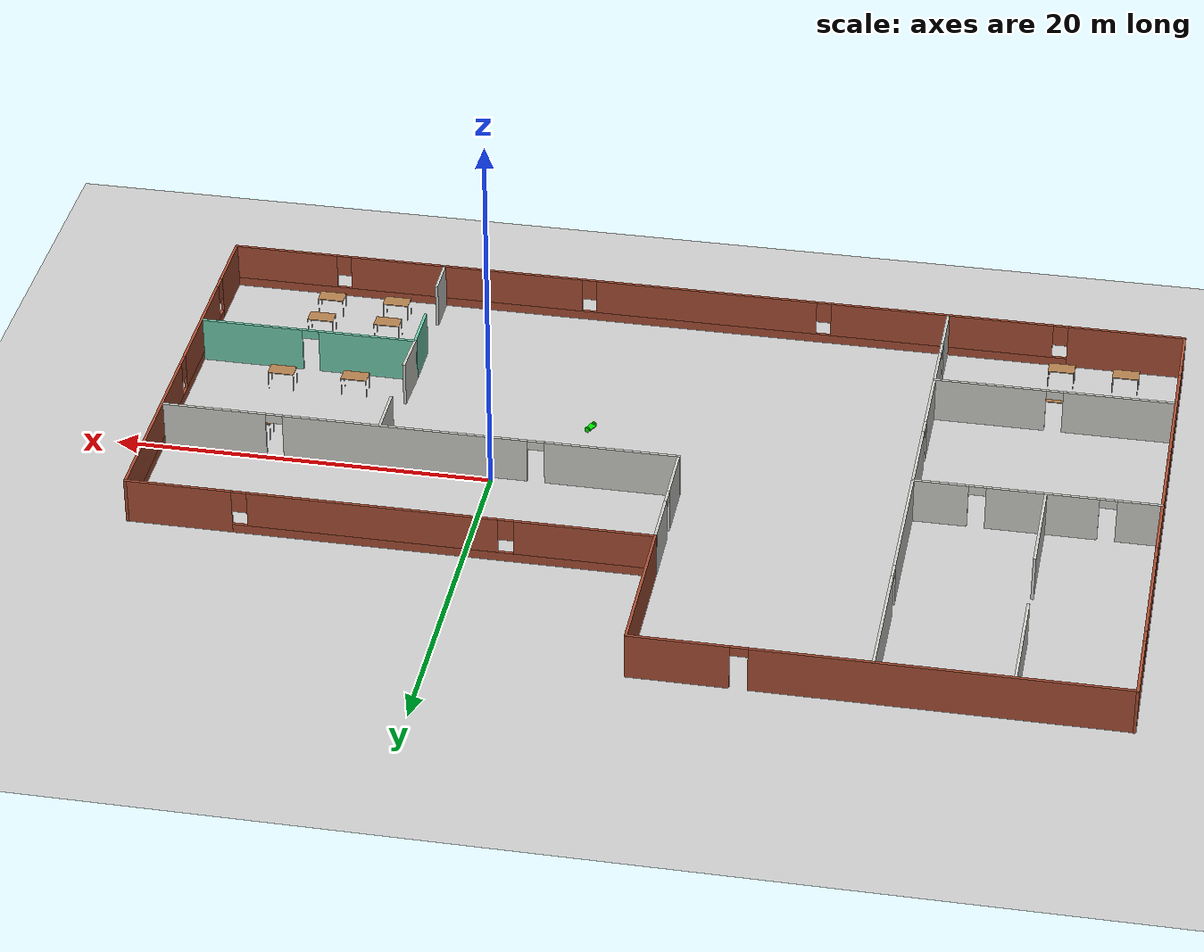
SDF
<sdf version="1.6">
 <world name="default">
  <plugin name="welcome_message" filename="libwelcome_message.so"/>
  <light name="sun" type="directional">
   <pose>0 0 10 0 -0 0</pose>
   <diffuse>0.8 0.8 0.8 1</diffuse>
   <specular>0.1 0.1 0.1 1</specular>
   <attenuation>
    <range>1000</range>
    <constant>0.9</constant>
    <linear>0.01</linear>
    <quadratic>0.001</quadratic>
   </attenuation>
   <direction>-0.5 0.5 -1</direction>
  </light>
  <model name="ground_plane">
   <static>1</static>
   <link name="link">
    <collision name="collision">
     <geometry><plane><normal>0 0 1</normal><size>100 100</size></plane></geometry>
     <surface><friction><ode><mu>100</mu><mu2>50</mu2></ode></friction></surface>
    </collision>
    <visual name="visual">
     <cast_shadows>0</cast_shadows>
     <geometry><plane><normal>0 0 1</normal><size>100 100</size></plane></geometry>
     <material>
      <script><uri>file://media/materials/scripts/gazebo.material</uri><name>Gazebo/Grey</name></script>
     </material>
    </visual>
   </link>
  </model>
  <gravity>0 0 -9.8</gravity>
  <magnetic_field>6e-06 2.3e-05 -4.2e-05</magnetic_field>
  <atmosphere type="adiabatic"/>
  <physics name="default_physics" default="0" type="ode">
   <max_step_size>0.001</max_step_size>
   <real_time_factor>1</real_time_factor>
   <real_time_update_rate>1000</real_time_update_rate>
  </physics>
  <scene><ambient>0.4 0.4 0.4 1</ambient><background>0.7 0.7 0.7 1</background><shadows>1</shadows></scene>
  <spherical_coordinates>
   <surface_model>EARTH_WGS84</surface_model>
   <latitude_deg>0</latitude_deg>
   <longitude_deg>0</longitude_deg>
   <elevation>0</elevation>
   <heading_deg>0</heading_deg>
  </spherical_coordinates>
  <model name="Building">
   <pose>-8.4819 -0.530793 0 0 -0 0</pose>
   <link name="Wall_11">
    <pose>-19.7067 0.118862 0 0 -0 0</pose>
    <visual name="Wall_11_Visual_0">
     <pose>-5.22567 0 1.25 0 -0 0</pose>
     <geometry><box><size>2.29865 0.15 2.5</size></box></geometry>
     <material>
      <script><uri>file://media/materials/scripts/gazebo.material</uri><name>Gazebo/CeilingTiled</name></script>
      <ambient>1 1 1 1</ambient>
     </material>
    </visual>
    <collision name="Wall_11_Collision_0">
     <geometry><box><size>2.29865 0.15 2.5</size></box></geometry>
     <pose>-5.22567 0 1.25 0 -0 0</pose>
    </collision>
    <visual name="Wall_11_Visual_1">
     <pose>-0.300767 0 1.25 0 -0 0</pose>
     <geometry><box><size>5.75116 0.15 2.5</size></box></geometry>
     <material>
      <script><uri>file://media/materials/scripts/gazebo.material</uri><name>Gazebo/CeilingTiled</name></script>
      <ambient>1 1 1 1</ambient>
     </material>
    </visual>
    <collision name="Wall_11_Collision_1">
     <geometry><box><size>5.75116 0.15 2.5</size></box></geometry>
     <pose>-0.300767 0 1.25 0 -0 0</pose>
    </collision>
    <visual name="Wall_11_Visual_2">
     <pose>4.92491 0 1.25 0 -0 0</pose>
     <geometry><box><size>2.90019 0.15 2.5</size></box></geometry>
     <material>
      <script><uri>file://media/materials/scripts/gazebo.material</uri><name>Gazebo/CeilingTiled</name></script>
      <ambient>1 1 1 1</ambient>
     </material>
    </visual>
    <collision name="Wall_11_Collision_2">
     <geometry><box><size>2.90019 0.15 2.5</size></box></geometry>
     <pose>4.92491 0 1.25 0 -0 0</pose>
    </collision>
    <visual name="Wall_11_Visual_3">
     <pose>-3.62635 0 2.25 0 -0 0</pose>
     <geometry><box><size>0.9 0.15 0.5</size></box></geometry>
     <material>
      <script><uri>file://media/materials/scripts/gazebo.material</uri><name>Gazebo/CeilingTiled</name></script>
      <ambient>1 1 1 1</ambient>
     </material>
    </visual>
    <collision name="Wall_11_Collision_3">
     <geometry><box><size>0.9 0.15 0.5</size></box></geometry>
     <pose>-3.62635 0 2.25 0 -0 0</pose>
    </collision>
    <visual name="Wall_11_Visual_4">
     <pose>3.02481 0 2.25 0 -0 0</pose>
     <geometry><box><size>0.9 0.15 0.5</size></box></geometry>
     <material>
      <script><uri>file://media/materials/scripts/gazebo.material</uri><name>Gazebo/CeilingTiled</name></script>
      <ambient>1 1 1 1</ambient>
     </material>
    </visual>
    <collision name="Wall_11_Collision_4">
     <geometry><box><size>0.9 0.15 0.5</size></box></geometry>
     <pose>3.02481 0 2.25 0 -0 0</pose>
    </collision>
   </link>
   <link name="Wall_13">
    <pose>-1.3 3.68488 0 0 0 -1.57082</pose>
    <visual name="Wall_13_Visual_0">
     <pose>-2.05181 0 1.25 0 -0 0</pose>
     <geometry><box><size>3.14637 0.15 2.5</size></box></geometry>
     <material>
      <script><uri>file://media/materials/scripts/gazebo.material</uri><name>Gazebo/CeilingTiled</name></script>
      <ambient>0.435294 0.796078 0.67451 1</ambient>
     </material>
    </visual>
    <collision name="Wall_13_Collision_0">
     <geometry><box><size>3.14637 0.15 2.5</size></box></geometry>
     <pose>-2.05181 0 1.25 0 -0 0</pose>
    </collision>
    <visual name="Wall_13_Visual_1">
     <pose>2.02319 0 1.25 0 -0 0</pose>
     <geometry><box><size>3.20363 0.15 2.5</size></box></geometry>
     <material>
      <script><uri>file://media/materials/scripts/gazebo.material</uri><name>Gazebo/CeilingTiled</name></script>
      <ambient>0.435294 0.796078 0.67451 1</ambient>
     </material>
    </visual>
    <collision name="Wall_13_Collision_1">
     <geometry><box><size>3.20363 0.15 2.5</size></box></geometry>
     <pose>2.02319 0 1.25 0 -0 0</pose>
    </collision>
    <visual name="Wall_13_Visual_2">
     <pose>-0.028629 0 2.25 0 -0 0</pose>
     <geometry><box><size>0.9 0.15 0.5</size></box></geometry>
     <material>
      <script><uri>file://media/materials/scripts/gazebo.material</uri><name>Gazebo/CeilingTiled</name></script>
      <ambient>0.435294 0.796078 0.67451 1</ambient>
     </material>
    </visual>
    <collision name="Wall_13_Collision_2">
     <geometry><box><size>0.9 0.15 0.5</size></box></geometry>
     <pose>-0.028629 0 2.25 0 -0 0</pose>
    </collision>
   </link>
   <link name="Wall_14">
    <pose>12.3749 0.134961 0 0 -0 0</pose>
    <visual name="Wall_14_Visual_0">
     <pose>-10.2012 0 1.25 0 -0 0</pose>
     <geometry><box><size>7.09767 0.15 2.5</size></box></geometry>
     <material>
      <script><uri>file://media/materials/scripts/gazebo.material</uri><name>Gazebo/CeilingTiled</name></script>
      <ambient>0.435294 0.796078 0.67451 1</ambient>
     </material>
    </visual>
    <collision name="Wall_14_Collision_0">
     <geometry><box><size>7.09767 0.15 2.5</size></box></geometry>
     <pose>-10.2012 0 1.25 0 -0 0</pose>
    </collision>
    <visual name="Wall_14_Visual_1">
     <pose>0.731858 0 1.25 0 -0 0</pose>
     <geometry><box><size>12.9684 0.15 2.5</size></box></geometry>
     <material>
      <script><uri>file://media/materials/scripts/gazebo.material</uri><name>Gazebo/CeilingTiled</name></script>
      <ambient>0.435294 0.796078 0.67451 1</ambient>
     </material>
    </visual>
    <collision name="Wall_14_Collision_1">
     <geometry><box><size>12.9684 0.15 2.5</size></box></geometry>
     <pose>0.731858 0 1.25 0 -0 0</pose>
    </collision>
    <visual name="Wall_14_Visual_2">
     <pose>10.933 0 1.25 0 -0 0</pose>
     <geometry><box><size>5.63395 0.15 2.5</size></box></geometry>
     <material>
      <script><uri>file://media/materials/scripts/gazebo.material</uri><name>Gazebo/CeilingTiled</name></script>
      <ambient>0.435294 0.796078 0.67451 1</ambient>
     </material>
    </visual>
    <collision name="Wall_14_Collision_2">
     <geometry><box><size>5.63395 0.15 2.5</size></box></geometry>
     <pose>10.933 0 1.25 0 -0 0</pose>
    </collision>
    <visual name="Wall_14_Visual_3">
     <pose>-6.20233 0 2.25 0 -0 0</pose>
     <geometry><box><size>0.9 0.15 0.5</size></box></geometry>
     <material>
      <script><uri>file://media/materials/scripts/gazebo.material</uri><name>Gazebo/CeilingTiled</name></script>
      <ambient>0.435294 0.796078 0.67451 1</ambient>
     </material>
    </visual>
    <collision name="Wall_14_Collision_3">
     <geometry><box><size>0.9 0.15 0.5</size></box></geometry>
     <pose>-6.20233 0 2.25 0 -0 0</pose>
    </collision>
    <visual name="Wall_14_Visual_4">
     <pose>7.66605 0 2.25 0 -0 0</pose>
     <geometry><box><size>0.9 0.15 0.5</size></box></geometry>
     <material>
      <script><uri>file://media/materials/scripts/gazebo.material</uri><name>Gazebo/CeilingTiled</name></script>
      <ambient>0.435294 0.796078 0.67451 1</ambient>
     </material>
    </visual>
    <collision name="Wall_14_Collision_4">
     <geometry><box><size>0.9 0.15 0.5</size></box></geometry>
     <pose>7.66605 0 2.25 0 -0 0</pose>
    </collision>
   </link>
   <link name="Wall_18">
    <pose>20.1246 -8.02227 0 0 -0 0</pose>
    <visual name="Wall_18_Visual_0">
     <pose>-3.20431 0 1.25 0 -0 0</pose>
     <geometry><box><size>5.34138 0.15 2.5</size></box></geometry>
     <material>
      <script><uri>file://media/materials/scripts/gazebo.material</uri><name>Gazebo/Grey</name></script>
      <ambient>0.435294 0.796078 0.67451 1</ambient>
     </material>
    </visual>
    <collision name="Wall_18_Collision_0">
     <geometry><box><size>5.34138 0.15 2.5</size></box></geometry>
     <pose>-3.20431 0 1.25 0 -0 0</pose>
    </collision>
    <visual name="Wall_18_Visual_1">
     <pose>3.12069 0 1.25 0 -0 0</pose>
     <geometry><box><size>5.50862 0.15 2.5</size></box></geometry>
     <material>
      <script><uri>file://media/materials/scripts/gazebo.material</uri><name>Gazebo/Grey</name></script>
      <ambient>0.435294 0.796078 0.67451 1</ambient>
     </material>
    </visual>
    <collision name="Wall_18_Collision_1">
     <geometry><box><size>5.50862 0.15 2.5</size></box></geometry>
     <pose>3.12069 0 1.25 0 -0 0</pose>
    </collision>
    <visual name="Wall_18_Visual_2">
     <pose>-0.083618 0 2.25 0 -0 0</pose>
     <geometry><box><size>0.9 0.15 0.5</size></box></geometry>
     <material>
      <script><uri>file://media/materials/scripts/gazebo.material</uri><name>Gazebo/Grey</name></script>
      <ambient>0.435294 0.796078 0.67451 1</ambient>
     </material>
    </visual>
    <collision name="Wall_18_Collision_2">
     <geometry><box><size>0.9 0.15 0.5</size></box></geometry>
     <pose>-0.083618 0 2.25 0 -0 0</pose>
    </collision>
   </link>
   <link name="Wall_2">
    <pose>-26.0501 0.075325 0 0 0 -1.5708</pose>
    <visual name="Wall_2_Visual_0">
     <pose>-13.5818 0 1.25 0 -0 0</pose>
     <geometry><box><size>4.08649 0.15 2.5</size></box></geometry>
     <material>
      <script><uri>file://media/materials/scripts/gazebo.material</uri><name>Gazebo/Bricks</name></script>
      <ambient>1 1 1 1</ambient>
     </material>
    </visual>
    <collision name="Wall_2_Collision_0">
     <geometry><box><size>4.08649 0.15 2.5</size></box></geometry>
     <pose>-13.5818 0 1.25 0 -0 0</pose>
    </collision>
    <visual name="Wall_2_Visual_1">
     <pose>2.04324 0 0.25 0 -0 0</pose>
     <geometry><box><size>27.1635 0.15 0.5</size></box></geometry>
     <material>
      <script><uri>file://media/materials/scripts/gazebo.material</uri><name>Gazebo/Bricks</name></script>
      <ambient>1 1 1 1</ambient>
     </material>
    </visual>
    <collision name="Wall_2_Collision_1">
     <geometry><box><size>27.1635 0.15 0.5</size></box></geometry>
     <pose>2.04324 0 0.25 0 -0 0</pose>
    </collision>
    <visual name="Wall_2_Visual_2">
     <pose>-7.63604 0 1.5 0 -0 0</pose>
     <geometry><box><size>6.20495 0.15 2</size></box></geometry>
     <material>
      <script><uri>file://media/materials/scripts/gazebo.material</uri><name>Gazebo/Bricks</name></script>
      <ambient>1 1 1 1</ambient>
     </material>
    </visual>
    <collision name="Wall_2_Collision_2">
     <geometry><box><size>6.20495 0.15 2</size></box></geometry>
     <pose>-7.63604 0 1.5 0 -0 0</pose>
    </collision>
    <visual name="Wall_2_Visual_3">
     <pose>0.147238 0 1.5 0 -0 0</pose>
     <geometry><box><size>7.7616 0.15 2</size></box></geometry>
     <material>
      <script><uri>file://media/materials/scripts/gazebo.material</uri><name>Gazebo/Bricks</name></script>
      <ambient>1 1 1 1</ambient>
     </material>
    </visual>
    <collision name="Wall_2_Collision_3">
     <geometry><box><size>7.7616 0.15 2</size></box></geometry>
     <pose>0.147238 0 1.5 0 -0 0</pose>
    </collision>
    <visual name="Wall_2_Visual_4">
     <pose>8.42581 0 1.5 0 -0 0</pose>
     <geometry><box><size>7.19555 0.15 2</size></box></geometry>
     <material>
      <script><uri>file://media/materials/scripts/gazebo.material</uri><name>Gazebo/Bricks</name></script>
      <ambient>1 1 1 1</ambient>
     </material>
    </visual>
    <collision name="Wall_2_Collision_4">
     <geometry><box><size>7.19555 0.15 2</size></box></geometry>
     <pose>8.42581 0 1.5 0 -0 0</pose>
    </collision>
    <visual name="Wall_2_Visual_5">
     <pose>14.2243 0 1.5 0 -0 0</pose>
     <geometry><box><size>2.80141 0.15 2</size></box></geometry>
     <material>
      <script><uri>file://media/materials/scripts/gazebo.material</uri><name>Gazebo/Bricks</name></script>
      <ambient>1 1 1 1</ambient>
     </material>
    </visual>
    <collision name="Wall_2_Collision_5">
     <geometry><box><size>2.80141 0.15 2</size></box></geometry>
     <pose>14.2243 0 1.5 0 -0 0</pose>
    </collision>
    <visual name="Wall_2_Visual_6">
     <pose>-11.1385 0 1.9 0 -0 0</pose>
     <geometry><box><size>0.8 0.15 1.2</size></box></geometry>
     <material>
      <script><uri>file://media/materials/scripts/gazebo.material</uri><name>Gazebo/Bricks</name></script>
      <ambient>1 1 1 1</ambient>
     </material>
    </visual>
    <collision name="Wall_2_Collision_6">
     <geometry><box><size>0.8 0.15 1.2</size></box></geometry>
     <pose>-11.1385 0 1.9 0 -0 0</pose>
    </collision>
    <visual name="Wall_2_Visual_7">
     <pose>-4.13356 0 1.9 0 -0 0</pose>
     <geometry><box><size>0.8 0.15 1.2</size></box></geometry>
     <material>
      <script><uri>file://media/materials/scripts/gazebo.material</uri><name>Gazebo/Bricks</name></script>
      <ambient>1 1 1 1</ambient>
     </material>
    </visual>
    <collision name="Wall_2_Collision_7">
     <geometry><box><size>0.8 0.15 1.2</size></box></geometry>
     <pose>-4.13356 0 1.9 0 -0 0</pose>
    </collision>
    <visual name="Wall_2_Visual_8">
     <pose>4.42804 0 1.9 0 -0 0</pose>
     <geometry><box><size>0.8 0.15 1.2</size></box></geometry>
     <material>
      <script><uri>file://media/materials/scripts/gazebo.material</uri><name>Gazebo/Bricks</name></script>
      <ambient>1 1 1 1</ambient>
     </material>
    </visual>
    <collision name="Wall_2_Collision_8">
     <geometry><box><size>0.8 0.15 1.2</size></box></geometry>
     <pose>4.42804 0 1.9 0 -0 0</pose>
    </collision>
    <visual name="Wall_2_Visual_9">
     <pose>12.4236 0 1.9 0 -0 0</pose>
     <geometry><box><size>0.8 0.15 1.2</size></box></geometry>
     <material>
      <script><uri>file://media/materials/scripts/gazebo.material</uri><name>Gazebo/Bricks</name></script>
      <ambient>1 1 1 1</ambient>
     </material>
    </visual>
    <collision name="Wall_2_Collision_9">
     <geometry><box><size>0.8 0.15 1.2</size></box></geometry>
     <pose>12.4236 0 1.9 0 -0 0</pose>
    </collision>
   </link>
   <link name="Wall_21">
    <collision name="Wall_21_Collision">
     <geometry><box><size>2.75 0.15 2.5</size></box></geometry>
     <pose>0 0 1.25 0 -0 0</pose>
    </collision>
    <visual name="Wall_21_Visual">
     <pose>0 0 1.25 0 -0 0</pose>
     <geometry><box><size>2.75 0.15 2.5</size></box></geometry>
     <material>
      <script><uri>file://media/materials/scripts/gazebo.material</uri><name>Gazebo/CeilingTiled</name></script>
      <ambient>0.435294 0.796078 0.67451 1</ambient>
     </material>
    </visual>
    <pose>14.4041 -1.23643 0 0 0 -1.5708</pose>
   </link>
   <link name="Wall_23">
    <collision name="Wall_23_Collision">
     <geometry><box><size>2.45989 0.15 2.5</size></box></geometry>
     <pose>0 0 1.25 0 -0 0</pose>
    </collision>
    <visual name="Wall_23_Visual">
     <pose>0 0 1.25 0 -0 0</pose>
     <geometry><box><size>2.45989 0.15 2.5</size></box></geometry>
     <material>
      <script><uri>file://media/materials/scripts/gazebo.material</uri><name>Gazebo/CeilingTiled</name></script>
      <ambient>0.435294 0.796078 0.67451 1</ambient>
     </material>
    </visual>
    <pose>14.3644 -6.86801 0 0 0 -1.60523</pose>
   </link>
   <link name="Wall_25">
    <collision name="Wall_25_Collision">
     <geometry><box><size>2.75 0.15 2.5</size></box></geometry>
     <pose>0 0 1.25 0 -0 0</pose>
    </collision>
    <visual name="Wall_25_Visual">
     <pose>0 0 1.25 0 -0 0</pose>
     <geometry><box><size>2.75 0.15 2.5</size></box></geometry>
     <material>
      <script><uri>file://media/materials/scripts/gazebo.material</uri><name>Gazebo/Grey</name></script>
      <ambient>0.435294 0.796078 0.67451 1</ambient>
     </material>
    </visual>
    <pose>14.3246 -9.32227 0 0 0 -1.5708</pose>
   </link>
   <link name="Wall_27">
    <collision name="Wall_27_Collision">
     <geometry><box><size>2.25 0.15 2.5</size></box></geometry>
     <pose>0 0 1.25 0 -0 0</pose>
    </collision>
    <visual name="Wall_27_Visual">
     <pose>0 0 1.25 0 -0 0</pose>
     <geometry><box><size>2.25 0.15 2.5</size></box></geometry>
     <material>
      <script><uri>file://media/materials/scripts/gazebo.material</uri><name>Gazebo/CeilingTiled</name></script>
      <ambient>0.435294 0.796078 0.67451 1</ambient>
     </material>
    </visual>
    <pose>14.3228 -14.5753 0 0 0 -1.5708</pose>
   </link>
   <link name="Wall_29">
    <collision name="Wall_29_Collision">
     <geometry><box><size>6 0.15 2.5</size></box></geometry>
     <pose>0 0 1.25 0 -0 0</pose>
    </collision>
    <visual name="Wall_29_Visual">
     <pose>0 0 1.25 0 -0 0</pose>
     <geometry><box><size>6 0.15 2.5</size></box></geometry>
     <material>
      <script><uri>file://media/materials/scripts/gazebo.material</uri><name>Gazebo/CeilingTiled</name></script>
      <ambient>1 1 1 1</ambient>
     </material>
    </visual>
    <pose>-20.2198 12.605 0 0 0 -1.5708</pose>
   </link>
   <link name="Wall_3">
    <pose>0.023328 -15.5683 0 0 0 -0.001798</pose>
    <visual name="Wall_3_Visual_0">
     <pose>-22.9832 0 1.25 0 -0 0</pose>
     <geometry><box><size>6.23696 0.15 2.5</size></box></geometry>
     <material>
      <script><uri>file://media/materials/scripts/gazebo.material</uri><name>Gazebo/Bricks</name></script>
      <ambient>1 1 1 1</ambient>
     </material>
    </visual>
    <collision name="Wall_3_Collision_0">
     <geometry><box><size>6.23696 0.15 2.5</size></box></geometry>
     <pose>-22.9832 0 1.25 0 -0 0</pose>
    </collision>
    <visual name="Wall_3_Visual_1">
     <pose>3.11848 0 0.25 0 -0 0</pose>
     <geometry><box><size>45.9663 0.15 0.5</size></box></geometry>
     <material>
      <script><uri>file://media/materials/scripts/gazebo.material</uri><name>Gazebo/Bricks</name></script>
      <ambient>1 1 1 1</ambient>
     </material>
    </visual>
    <collision name="Wall_3_Collision_1">
     <geometry><box><size>45.9663 0.15 0.5</size></box></geometry>
     <pose>3.11848 0 0.25 0 -0 0</pose>
    </collision>
    <visual name="Wall_3_Visual_2">
     <pose>-13.0612 0 1.5 0 -0 0</pose>
     <geometry><box><size>12.007 0.15 2</size></box></geometry>
     <material>
      <script><uri>file://media/materials/scripts/gazebo.material</uri><name>Gazebo/Bricks</name></script>
      <ambient>1 1 1 1</ambient>
     </material>
    </visual>
    <collision name="Wall_3_Collision_2">
     <geometry><box><size>12.007 0.15 2</size></box></geometry>
     <pose>-13.0612 0 1.5 0 -0 0</pose>
    </collision>
    <visual name="Wall_3_Visual_3">
     <pose>-0.218864 0 1.5 0 -0 0</pose>
     <geometry><box><size>12.0776 0.15 2</size></box></geometry>
     <material>
      <script><uri>file://media/materials/scripts/gazebo.material</uri><name>Gazebo/Bricks</name></script>
      <ambient>1 1 1 1</ambient>
     </material>
    </visual>
    <collision name="Wall_3_Collision_3">
     <geometry><box><size>12.0776 0.15 2</size></box></geometry>
     <pose>-0.218864 0 1.5 0 -0 0</pose>
    </collision>
    <visual name="Wall_3_Visual_4">
     <pose>13.0836 0 1.5 0 -0 0</pose>
     <geometry><box><size>12.9272 0.15 2</size></box></geometry>
     <material>
      <script><uri>file://media/materials/scripts/gazebo.material</uri><name>Gazebo/Bricks</name></script>
      <ambient>1 1 1 1</ambient>
     </material>
    </visual>
    <collision name="Wall_3_Collision_4">
     <geometry><box><size>12.9272 0.15 2</size></box></geometry>
     <pose>13.0836 0 1.5 0 -0 0</pose>
    </collision>
    <visual name="Wall_3_Visual_5">
     <pose>23.2244 0 1.5 0 -0 0</pose>
     <geometry><box><size>5.75446 0.15 2</size></box></geometry>
     <material>
      <script><uri>file://media/materials/scripts/gazebo.material</uri><name>Gazebo/Bricks</name></script>
      <ambient>1 1 1 1</ambient>
     </material>
    </visual>
    <collision name="Wall_3_Collision_5">
     <geometry><box><size>5.75446 0.15 2</size></box></geometry>
     <pose>23.2244 0 1.5 0 -0 0</pose>
    </collision>
    <visual name="Wall_3_Visual_6">
     <pose>-19.4647 0 1.9 0 -0 0</pose>
     <geometry><box><size>0.8 0.15 1.2</size></box></geometry>
     <material>
      <script><uri>file://media/materials/scripts/gazebo.material</uri><name>Gazebo/Bricks</name></script>
      <ambient>1 1 1 1</ambient>
     </material>
    </visual>
    <collision name="Wall_3_Collision_6">
     <geometry><box><size>0.8 0.15 1.2</size></box></geometry>
     <pose>-19.4647 0 1.9 0 -0 0</pose>
    </collision>
    <visual name="Wall_3_Visual_7">
     <pose>-6.65768 0 1.9 0 -0 0</pose>
     <geometry><box><size>0.8 0.15 1.2</size></box></geometry>
     <material>
      <script><uri>file://media/materials/scripts/gazebo.material</uri><name>Gazebo/Bricks</name></script>
      <ambient>1 1 1 1</ambient>
     </material>
    </visual>
    <collision name="Wall_3_Collision_7">
     <geometry><box><size>0.8 0.15 1.2</size></box></geometry>
     <pose>-6.65768 0 1.9 0 -0 0</pose>
    </collision>
    <visual name="Wall_3_Visual_8">
     <pose>6.21995 0 1.9 0 -0 0</pose>
     <geometry><box><size>0.8 0.15 1.2</size></box></geometry>
     <material>
      <script><uri>file://media/materials/scripts/gazebo.material</uri><name>Gazebo/Bricks</name></script>
      <ambient>1 1 1 1</ambient>
     </material>
    </visual>
    <collision name="Wall_3_Collision_8">
     <geometry><box><size>0.8 0.15 1.2</size></box></geometry>
     <pose>6.21995 0 1.9 0 -0 0</pose>
    </collision>
    <visual name="Wall_3_Visual_9">
     <pose>19.9472 0 1.9 0 -0 0</pose>
     <geometry><box><size>0.8 0.15 1.2</size></box></geometry>
     <material>
      <script><uri>file://media/materials/scripts/gazebo.material</uri><name>Gazebo/Bricks</name></script>
      <ambient>1 1 1 1</ambient>
     </material>
    </visual>
    <collision name="Wall_3_Collision_9">
     <geometry><box><size>0.8 0.15 1.2</size></box></geometry>
     <pose>19.9472 0 1.9 0 -0 0</pose>
    </collision>
   </link>
   <link name="Wall_32">
    <collision name="Wall_32_Collision">
     <geometry><box><size>5.75 0.15 2.5</size></box></geometry>
     <pose>0 0 1.25 0 -0 0</pose>
    </collision>
    <visual name="Wall_32_Visual">
     <pose>0 0 1.25 0 -0 0</pose>
     <geometry><box><size>5.75 0.15 2.5</size></box></geometry>
     <material>
      <script><uri>file://media/materials/scripts/gazebo.material</uri><name>Gazebo/CeilingTiled</name></script>
      <ambient>1 1 1 1</ambient>
     </material>
    </visual>
    <pose>-20.149 2.96555 0 0 0 -1.5708</pose>
   </link>
   <link name="Wall_34">
    <pose>-19.7219 -9.23495 0 0 -0 0</pose>
    <visual name="Wall_34_Visual_0">
     <pose>-3.41381 0 1.25 0 -0 0</pose>
     <geometry><box><size>5.92238 0.15 2.5</size></box></geometry>
     <material>
      <script><uri>file://media/materials/scripts/gazebo.material</uri><name>Gazebo/CeilingTiled</name></script>
      <ambient>1 1 1 1</ambient>
     </material>
    </visual>
    <collision name="Wall_34_Collision_0">
     <geometry><box><size>5.92238 0.15 2.5</size></box></geometry>
     <pose>-3.41381 0 1.25 0 -0 0</pose>
    </collision>
    <visual name="Wall_34_Visual_1">
     <pose>3.41119 0 1.25 0 -0 0</pose>
     <geometry><box><size>5.92762 0.15 2.5</size></box></geometry>
     <material>
      <script><uri>file://media/materials/scripts/gazebo.material</uri><name>Gazebo/CeilingTiled</name></script>
      <ambient>1 1 1 1</ambient>
     </material>
    </visual>
    <collision name="Wall_34_Collision_1">
     <geometry><box><size>5.92762 0.15 2.5</size></box></geometry>
     <pose>3.41119 0 1.25 0 -0 0</pose>
    </collision>
    <visual name="Wall_34_Visual_2">
     <pose>-0.002623 0 2.25 0 -0 0</pose>
     <geometry><box><size>0.9 0.15 0.5</size></box></geometry>
     <material>
      <script><uri>file://media/materials/scripts/gazebo.material</uri><name>Gazebo/CeilingTiled</name></script>
      <ambient>1 1 1 1</ambient>
     </material>
    </visual>
    <collision name="Wall_34_Collision_2">
     <geometry><box><size>0.9 0.15 0.5</size></box></geometry>
     <pose>-0.002623 0 2.25 0 -0 0</pose>
    </collision>
   </link>
   <link name="Wall_4">
    <pose>26.0499 -4.19004 0 0 -0 1.5708</pose>
    <visual name="Wall_4_Visual_0">
     <pose>-9.74608 0 1.25 0 -0 0</pose>
     <geometry><box><size>3.50783 0.15 2.5</size></box></geometry>
     <material>
      <script><uri>file://media/materials/scripts/gazebo.material</uri><name>Gazebo/Bricks</name></script>
      <ambient>1 1 1 1</ambient>
     </material>
    </visual>
    <collision name="Wall_4_Collision_0">
     <geometry><box><size>3.50783 0.15 2.5</size></box></geometry>
     <pose>-9.74608 0 1.25 0 -0 0</pose>
    </collision>
    <visual name="Wall_4_Visual_1">
     <pose>1.75392 0 0.25 0 -0 0</pose>
     <geometry><box><size>19.4922 0.15 0.5</size></box></geometry>
     <material>
      <script><uri>file://media/materials/scripts/gazebo.material</uri><name>Gazebo/Bricks</name></script>
      <ambient>1 1 1 1</ambient>
     </material>
    </visual>
    <collision name="Wall_4_Collision_1">
     <geometry><box><size>19.4922 0.15 0.5</size></box></geometry>
     <pose>1.75392 0 0.25 0 -0 0</pose>
    </collision>
    <visual name="Wall_4_Visual_2">
     <pose>-3.70053 0 1.5 0 -0 0</pose>
     <geometry><box><size>6.98328 0.15 2</size></box></geometry>
     <material>
      <script><uri>file://media/materials/scripts/gazebo.material</uri><name>Gazebo/Bricks</name></script>
      <ambient>1 1 1 1</ambient>
     </material>
    </visual>
    <collision name="Wall_4_Collision_2">
     <geometry><box><size>6.98328 0.15 2</size></box></geometry>
     <pose>-3.70053 0 1.5 0 -0 0</pose>
    </collision>
    <visual name="Wall_4_Visual_3">
     <pose>6.04556 0 1.5 0 -0 0</pose>
     <geometry><box><size>10.9089 0.15 2</size></box></geometry>
     <material>
      <script><uri>file://media/materials/scripts/gazebo.material</uri><name>Gazebo/Bricks</name></script>
      <ambient>1 1 1 1</ambient>
     </material>
    </visual>
    <collision name="Wall_4_Collision_3">
     <geometry><box><size>10.9089 0.15 2</size></box></geometry>
     <pose>6.04556 0 1.5 0 -0 0</pose>
    </collision>
    <visual name="Wall_4_Visual_4">
     <pose>-7.59217 0 1.9 0 -0 0</pose>
     <geometry><box><size>0.8 0.15 1.2</size></box></geometry>
     <material>
      <script><uri>file://media/materials/scripts/gazebo.material</uri><name>Gazebo/Bricks</name></script>
      <ambient>1 1 1 1</ambient>
     </material>
    </visual>
    <collision name="Wall_4_Collision_4">
     <geometry><box><size>0.8 0.15 1.2</size></box></geometry>
     <pose>-7.59217 0 1.9 0 -0 0</pose>
    </collision>
    <visual name="Wall_4_Visual_5">
     <pose>0.19111 0 1.9 0 -0 0</pose>
     <geometry><box><size>0.8 0.15 1.2</size></box></geometry>
     <material>
      <script><uri>file://media/materials/scripts/gazebo.material</uri><name>Gazebo/Bricks</name></script>
      <ambient>1 1 1 1</ambient>
     </material>
    </visual>
    <collision name="Wall_4_Collision_5">
     <geometry><box><size>0.8 0.15 1.2</size></box></geometry>
     <pose>0.19111 0 1.9 0 -0 0</pose>
    </collision>
   </link>
   <link name="Wall_5">
    <pose>12.375 7.23488 0 0 0 -3.14159</pose>
    <visual name="Wall_5_Visual_0">
     <pose>-10.9434 0 1.25 0 -0 0</pose>
     <geometry><box><size>5.61323 0.15 2.5</size></box></geometry>
     <material>
      <script><uri>file://media/materials/scripts/gazebo.material</uri><name>Gazebo/Bricks</name></script>
      <ambient>1 1 1 1</ambient>
     </material>
    </visual>
    <collision name="Wall_5_Collision_0">
     <geometry><box><size>5.61323 0.15 2.5</size></box></geometry>
     <pose>-10.9434 0 1.25 0 -0 0</pose>
    </collision>
    <visual name="Wall_5_Visual_1">
     <pose>2.80662 0 0.25 0 -0 0</pose>
     <geometry><box><size>21.8868 0.15 0.5</size></box></geometry>
     <material>
      <script><uri>file://media/materials/scripts/gazebo.material</uri><name>Gazebo/Bricks</name></script>
      <ambient>1 1 1 1</ambient>
     </material>
    </visual>
    <collision name="Wall_5_Collision_1">
     <geometry><box><size>21.8868 0.15 0.5</size></box></geometry>
     <pose>2.80662 0 0.25 0 -0 0</pose>
    </collision>
    <visual name="Wall_5_Visual_2">
     <pose>-0.837989 0 1.5 0 -0 0</pose>
     <geometry><box><size>12.9976 0.15 2</size></box></geometry>
     <material>
      <script><uri>file://media/materials/scripts/gazebo.material</uri><name>Gazebo/Bricks</name></script>
      <ambient>1 1 1 1</ambient>
     </material>
    </visual>
    <collision name="Wall_5_Collision_2">
     <geometry><box><size>12.9976 0.15 2</size></box></geometry>
     <pose>-0.837989 0 1.5 0 -0 0</pose>
    </collision>
    <visual name="Wall_5_Visual_3">
     <pose>10.1054 0 1.5 0 -0 0</pose>
     <geometry><box><size>7.28921 0.15 2</size></box></geometry>
     <material>
      <script><uri>file://media/materials/scripts/gazebo.material</uri><name>Gazebo/Bricks</name></script>
      <ambient>1 1 1 1</ambient>
     </material>
    </visual>
    <collision name="Wall_5_Collision_3">
     <geometry><box><size>7.28921 0.15 2</size></box></geometry>
     <pose>10.1054 0 1.5 0 -0 0</pose>
    </collision>
    <visual name="Wall_5_Visual_4">
     <pose>-7.73677 0 1.9 0 -0 0</pose>
     <geometry><box><size>0.8 0.15 1.2</size></box></geometry>
     <material>
      <script><uri>file://media/materials/scripts/gazebo.material</uri><name>Gazebo/Bricks</name></script>
      <ambient>1 1 1 1</ambient>
     </material>
    </visual>
    <collision name="Wall_5_Collision_4">
     <geometry><box><size>0.8 0.15 1.2</size></box></geometry>
     <pose>-7.73677 0 1.9 0 -0 0</pose>
    </collision>
    <visual name="Wall_5_Visual_5">
     <pose>6.06079 0 1.9 0 -0 0</pose>
     <geometry><box><size>0.8 0.15 1.2</size></box></geometry>
     <material>
      <script><uri>file://media/materials/scripts/gazebo.material</uri><name>Gazebo/Bricks</name></script>
      <ambient>1 1 1 1</ambient>
     </material>
    </visual>
    <collision name="Wall_5_Collision_5">
     <geometry><box><size>0.8 0.15 1.2</size></box></geometry>
     <pose>6.06079 0 1.9 0 -0 0</pose>
    </collision>
   </link>
   <link name="Wall_6">
    <collision name="Wall_6_Collision">
     <geometry><box><size>8.5 0.15 2.5</size></box></geometry>
     <pose>0 0 1.25 0 -0 0</pose>
    </collision>
    <visual name="Wall_6_Visual">
     <pose>0 0 1.25 0 -0 0</pose>
     <geometry><box><size>8.5 0.15 2.5</size></box></geometry>
     <material>
      <script><uri>file://media/materials/scripts/gazebo.material</uri><name>Gazebo/Bricks</name></script>
      <ambient>1 1 1 1</ambient>
     </material>
    </visual>
    <pose>-1.29993 11.4098 0 0 -0 1.5708</pose>
   </link>
   <link name="Wall_7">
    <pose>-13.6 15.5849 0 0 -0 3.14159</pose>
    <visual name="Wall_7_Visual_0">
     <pose>-9.7892 0 1.25 0 -0 0</pose>
     <geometry><box><size>5.17159 0.15 2.5</size></box></geometry>
     <material>
      <script><uri>file://media/materials/scripts/gazebo.material</uri><name>Gazebo/Bricks</name></script>
      <ambient>1 1 1 1</ambient>
     </material>
    </visual>
    <collision name="Wall_7_Collision_0">
     <geometry><box><size>5.17159 0.15 2.5</size></box></geometry>
     <pose>-9.7892 0 1.25 0 -0 0</pose>
    </collision>
    <visual name="Wall_7_Visual_1">
     <pose>3.0358 0 1.25 0 -0 0</pose>
     <geometry><box><size>18.6784 0.15 2.5</size></box></geometry>
     <material>
      <script><uri>file://media/materials/scripts/gazebo.material</uri><name>Gazebo/Bricks</name></script>
      <ambient>1 1 1 1</ambient>
     </material>
    </visual>
    <collision name="Wall_7_Collision_1">
     <geometry><box><size>18.6784 0.15 2.5</size></box></geometry>
     <pose>3.0358 0 1.25 0 -0 0</pose>
    </collision>
    <visual name="Wall_7_Visual_2">
     <pose>-6.75341 0 2.25 0 -0 0</pose>
     <geometry><box><size>0.9 0.15 0.5</size></box></geometry>
     <material>
      <script><uri>file://media/materials/scripts/gazebo.material</uri><name>Gazebo/Bricks</name></script>
      <ambient>1 1 1 1</ambient>
     </material>
    </visual>
    <collision name="Wall_7_Collision_2">
     <geometry><box><size>0.9 0.15 0.5</size></box></geometry>
     <pose>-6.75341 0 2.25 0 -0 0</pose>
    </collision>
   </link>
   <link name="Wall_9">
    <pose>-13.374 0.008937 0 0 0 -1.5708</pose>
    <visual name="Wall_9_Visual_0">
     <pose>-12.0479 0 1.25 0 -0 0</pose>
     <geometry><box><size>7.15417 0.15 2.5</size></box></geometry>
     <material>
      <script><uri>file://media/materials/scripts/gazebo.material</uri><name>Gazebo/CeilingTiled</name></script>
      <ambient>1 1 1 1</ambient>
     </material>
    </visual>
    <collision name="Wall_9_Collision_0">
     <geometry><box><size>7.15417 0.15 2.5</size></box></geometry>
     <pose>-12.0479 0 1.25 0 -0 0</pose>
    </collision>
    <visual name="Wall_9_Visual_1">
     <pose>-1.61732 0 1.25 0 -0 0</pose>
     <geometry><box><size>11.907 0.15 2.5</size></box></geometry>
     <material>
      <script><uri>file://media/materials/scripts/gazebo.material</uri><name>Gazebo/CeilingTiled</name></script>
      <ambient>1 1 1 1</ambient>
     </material>
    </visual>
    <collision name="Wall_9_Collision_1">
     <geometry><box><size>11.907 0.15 2.5</size></box></geometry>
     <pose>-1.61732 0 1.25 0 -0 0</pose>
    </collision>
    <visual name="Wall_9_Visual_2">
     <pose>8.53632 0 1.25 0 -0 0</pose>
     <geometry><box><size>6.60025 0.15 2.5</size></box></geometry>
     <material>
      <script><uri>file://media/materials/scripts/gazebo.material</uri><name>Gazebo/CeilingTiled</name></script>
      <ambient>1 1 1 1</ambient>
     </material>
    </visual>
    <collision name="Wall_9_Collision_2">
     <geometry><box><size>6.60025 0.15 2.5</size></box></geometry>
     <pose>8.53632 0 1.25 0 -0 0</pose>
    </collision>
    <visual name="Wall_9_Visual_3">
     <pose>14.1807 0 1.25 0 -0 0</pose>
     <geometry><box><size>2.88856 0.15 2.5</size></box></geometry>
     <material>
      <script><uri>file://media/materials/scripts/gazebo.material</uri><name>Gazebo/CeilingTiled</name></script>
      <ambient>1 1 1 1</ambient>
     </material>
    </visual>
    <collision name="Wall_9_Collision_3">
     <geometry><box><size>2.88856 0.15 2.5</size></box></geometry>
     <pose>14.1807 0 1.25 0 -0 0</pose>
    </collision>
    <visual name="Wall_9_Visual_4">
     <pose>-8.02083 0 2.25 0 -0 0</pose>
     <geometry><box><size>0.9 0.15 0.5</size></box></geometry>
     <material>
      <script><uri>file://media/materials/scripts/gazebo.material</uri><name>Gazebo/CeilingTiled</name></script>
      <ambient>1 1 1 1</ambient>
     </material>
    </visual>
    <collision name="Wall_9_Collision_4">
     <geometry><box><size>0.9 0.15 0.5</size></box></geometry>
     <pose>-8.02083 0 2.25 0 -0 0</pose>
    </collision>
    <visual name="Wall_9_Visual_5">
     <pose>4.78619 0 2.25 0 -0 0</pose>
     <geometry><box><size>0.9 0.15 0.5</size></box></geometry>
     <material>
      <script><uri>file://media/materials/scripts/gazebo.material</uri><name>Gazebo/CeilingTiled</name></script>
      <ambient>1 1 1 1</ambient>
     </material>
    </visual>
    <collision name="Wall_9_Collision_5">
     <geometry><box><size>0.9 0.15 0.5</size></box></geometry>
     <pose>4.78619 0 2.25 0 -0 0</pose>
    </collision>
    <visual name="Wall_9_Visual_6">
     <pose>12.2864 0 2.25 0 -0 0</pose>
     <geometry><box><size>0.9 0.15 0.5</size></box></geometry>
     <material>
      <script><uri>file://media/materials/scripts/gazebo.material</uri><name>Gazebo/CeilingTiled</name></script>
      <ambient>1 1 1 1</ambient>
     </material>
    </visual>
    <collision name="Wall_9_Collision_6">
     <geometry><box><size>0.9 0.15 0.5</size></box></geometry>
     <pose>12.2864 0 2.25 0 -0 0</pose>
    </collision>
   </link>
   <static>1</static>
  </model>
  <model name="table">
   <static>0</static>
   <link name="link">
    <collision name="surface">
     <pose>0 0 1 0 -0 0</pose>
     <geometry><box><size>1.5 0.8 0.03</size></box></geometry>
     <surface><friction><ode><mu>0.6</mu><mu2>0.6</mu2></ode></friction></surface>
    </collision>
    <visual name="visual1">
     <pose>0 0 1 0 -0 0</pose>
     <geometry><box><size>1.4 0.8 0.04</size></box></geometry>
     <material>
      <script><uri>file://media/materials/scripts/gazebo.material</uri><name>Gazebo/Wood</name></script>
     </material>
    </visual>
    <collision name="front_left_leg">
     <pose>0.68 0.38 0.5 0 -0 0</pose>
     <geometry><cylinder><radius>0.02</radius><length>1</length></cylinder></geometry>
    </collision>
    <visual name="front_left_leg">
     <pose>0.68 0.38 0.5 0 -0 0</pose>
     <geometry><cylinder><radius>0.02</radius><length>1</length></cylinder></geometry>
     <material>
      <script><uri>file://media/materials/scripts/gazebo.material</uri><name>Gazebo/Grey</name></script>
     </material>
    </visual>
    <collision name="front_right_leg">
     <pose>0.68 -0.38 0.5 0 -0 0</pose>
     <geometry><cylinder><radius>0.02</radius><length>1</length></cylinder></geometry>
    </collision>
    <visual name="front_right_leg">
     <pose>0.68 -0.38 0.5 0 -0 0</pose>
     <geometry><cylinder><radius>0.02</radius><length>1</length></cylinder></geometry>
     <material>
      <script><uri>file://media/materials/scripts/gazebo.material</uri><name>Gazebo/Grey</name></script>
     </material>
    </visual>
    <collision name="back_right_leg">
     <pose>-0.68 -0.38 0.5 0 -0 0</pose>
     <geometry><cylinder><radius>0.02</radius><length>1</length></cylinder></geometry>
    </collision>
    <visual name="back_right_leg">
     <pose>-0.68 -0.38 0.5 0 -0 0</pose>
     <geometry><cylinder><radius>0.02</radius><length>1</length></cylinder></geometry>
     <material>
      <script><uri>file://media/materials/scripts/gazebo.material</uri><name>Gazebo/Grey</name></script>
     </material>
    </visual>
    <collision name="back_left_leg">
     <pose>-0.68 0.38 0.5 0 -0 0</pose>
     <geometry><cylinder><radius>0.02</radius><length>1</length></cylinder></geometry>
    </collision>
    <visual name="back_left_leg">
     <pose>-0.68 0.38 0.5 0 -0 0</pose>
     <geometry><cylinder><radius>0.02</radius><length>1</length></cylinder></geometry>
     <material>
      <script><uri>file://media/materials/scripts/gazebo.material</uri><name>Gazebo/Grey</name></script>
     </material>
    </visual>
    <inertial>
     <inertia><ixx>1</ixx><ixy>0</ixy><ixz>0</ixz><iyy>1</iyy><iyz>0</iyz><izz>1</izz></inertia>
     <mass>1</mass>
    </inertial>
   </link>
   <pose>8.17547 -14.4149 -9e-06 0 -1e-06 0</pose>
  </model>
  <model name="table_0">
   <static>0</static>
   <link name="link">
    <collision name="surface">
     <pose>0 0 1 0 -0 0</pose>
     <geometry><box><size>1.5 0.8 0.03</size></box></geometry>
     <surface><friction><ode><mu>0.6</mu><mu2>0.6</mu2></ode></friction></surface>
    </collision>
    <visual name="visual1">
     <pose>0 0 1 0 -0 0</pose>
     <geometry><box><size>1.4 0.8 0.04</size></box></geometry>
     <material>
      <script><uri>file://media/materials/scripts/gazebo.material</uri><name>Gazebo/Wood</name></script>
     </material>
    </visual>
    <collision name="front_left_leg">
     <pose>0.68 0.38 0.5 0 -0 0</pose>
     <geometry><cylinder><radius>0.02</radius><length>1</length></cylinder></geometry>
    </collision>
    <visual name="front_left_leg">
     <pose>0.68 0.38 0.5 0 -0 0</pose>
     <geometry><cylinder><radius>0.02</radius><length>1</length></cylinder></geometry>
     <material>
      <script><uri>file://media/materials/scripts/gazebo.material</uri><name>Gazebo/Grey</name></script>
     </material>
    </visual>
    <collision name="front_right_leg">
     <pose>0.68 -0.38 0.5 0 -0 0</pose>
     <geometry><cylinder><radius>0.02</radius><length>1</length></cylinder></geometry>
    </collision>
    <visual name="front_right_leg">
     <pose>0.68 -0.38 0.5 0 -0 0</pose>
     <geometry><cylinder><radius>0.02</radius><length>1</length></cylinder></geometry>
     <material>
      <script><uri>file://media/materials/scripts/gazebo.material</uri><name>Gazebo/Grey</name></script>
     </material>
    </visual>
    <collision name="back_right_leg">
     <pose>-0.68 -0.38 0.5 0 -0 0</pose>
     <geometry><cylinder><radius>0.02</radius><length>1</length></cylinder></geometry>
    </collision>
    <visual name="back_right_leg">
     <pose>-0.68 -0.38 0.5 0 -0 0</pose>
     <geometry><cylinder><radius>0.02</radius><length>1</length></cylinder></geometry>
     <material>
      <script><uri>file://media/materials/scripts/gazebo.material</uri><name>Gazebo/Grey</name></script>
     </material>
    </visual>
    <collision name="back_left_leg">
     <pose>-0.68 0.38 0.5 0 -0 0</pose>
     <geometry><cylinder><radius>0.02</radius><length>1</length></cylinder></geometry>
    </collision>
    <visual name="back_left_leg">
     <pose>-0.68 0.38 0.5 0 -0 0</pose>
     <geometry><cylinder><radius>0.02</radius><length>1</length></cylinder></geometry>
     <material>
      <script><uri>file://media/materials/scripts/gazebo.material</uri><name>Gazebo/Grey</name></script>
     </material>
    </visual>
    <inertial>
     <inertia><ixx>1</ixx><ixy>0</ixy><ixz>0</ixz><iyy>1</iyy><iyz>0</iyz><izz>1</izz></inertia>
     <mass>1</mass>
    </inertial>
   </link>
   <pose>8.22446 -12.3428 -9e-06 0 -1e-06 0</pose>
  </model>
  <model name="table_1">
   <static>0</static>
   <link name="link">
    <collision name="surface">
     <pose>0 0 1 0 -0 0</pose>
     <geometry><box><size>1.5 0.8 0.03</size></box></geometry>
     <surface><friction><ode><mu>0.6</mu><mu2>0.6</mu2></ode></friction></surface>
    </collision>
    <visual name="visual1">
     <pose>0 0 1 0 -0 0</pose>
     <geometry><box><size>1.4 0.8 0.04</size></box></geometry>
     <material>
      <script><uri>file://media/materials/scripts/gazebo.material</uri><name>Gazebo/Wood</name></script>
     </material>
    </visual>
    <collision name="front_left_leg">
     <pose>0.68 0.38 0.5 0 -0 0</pose>
     <geometry><cylinder><radius>0.02</radius><length>1</length></cylinder></geometry>
    </collision>
    <visual name="front_left_leg">
     <pose>0.68 0.38 0.5 0 -0 0</pose>
     <geometry><cylinder><radius>0.02</radius><length>1</length></cylinder></geometry>
     <material>
      <script><uri>file://media/materials/scripts/gazebo.material</uri><name>Gazebo/Grey</name></script>
     </material>
    </visual>
    <collision name="front_right_leg">
     <pose>0.68 -0.38 0.5 0 -0 0</pose>
     <geometry><cylinder><radius>0.02</radius><length>1</length></cylinder></geometry>
    </collision>
    <visual name="front_right_leg">
     <pose>0.68 -0.38 0.5 0 -0 0</pose>
     <geometry><cylinder><radius>0.02</radius><length>1</length></cylinder></geometry>
     <material>
      <script><uri>file://media/materials/scripts/gazebo.material</uri><name>Gazebo/Grey</name></script>
     </material>
    </visual>
    <collision name="back_right_leg">
     <pose>-0.68 -0.38 0.5 0 -0 0</pose>
     <geometry><cylinder><radius>0.02</radius><length>1</length></cylinder></geometry>
    </collision>
    <visual name="back_right_leg">
     <pose>-0.68 -0.38 0.5 0 -0 0</pose>
     <geometry><cylinder><radius>0.02</radius><length>1</length></cylinder></geometry>
     <material>
      <script><uri>file://media/materials/scripts/gazebo.material</uri><name>Gazebo/Grey</name></script>
     </material>
    </visual>
    <collision name="back_left_leg">
     <pose>-0.68 0.38 0.5 0 -0 0</pose>
     <geometry><cylinder><radius>0.02</radius><length>1</length></cylinder></geometry>
    </collision>
    <visual name="back_left_leg">
     <pose>-0.68 0.38 0.5 0 -0 0</pose>
     <geometry><cylinder><radius>0.02</radius><length>1</length></cylinder></geometry>
     <material>
      <script><uri>file://media/materials/scripts/gazebo.material</uri><name>Gazebo/Grey</name></script>
     </material>
    </visual>
    <inertial>
     <inertia><ixx>1</ixx><ixy>0</ixy><ixz>0</ixz><iyy>1</iyy><iyz>0</iyz><izz>1</izz></inertia>
     <mass>1</mass>
    </inertial>
   </link>
   <pose>11.7764 -14.2937 -9e-06 0 -1e-06 0</pose>
  </model>
  <model name="table_2">
   <static>0</static>
   <link name="link">
    <collision name="surface">
     <pose>0 0 1 0 -0 0</pose>
     <geometry><box><size>1.5 0.8 0.03</size></box></geometry>
     <surface><friction><ode><mu>0.6</mu><mu2>0.6</mu2></ode></friction></surface>
    </collision>
    <visual name="visual1">
     <pose>0 0 1 0 -0 0</pose>
     <geometry><box><size>1.4 0.8 0.04</size></box></geometry>
     <material>
      <script><uri>file://media/materials/scripts/gazebo.material</uri><name>Gazebo/Wood</name></script>
     </material>
    </visual>
    <collision name="front_left_leg">
     <pose>0.68 0.38 0.5 0 -0 0</pose>
     <geometry><cylinder><radius>0.02</radius><length>1</length></cylinder></geometry>
    </collision>
    <visual name="front_left_leg">
     <pose>0.68 0.38 0.5 0 -0 0</pose>
     <geometry><cylinder><radius>0.02</radius><length>1</length></cylinder></geometry>
     <material>
      <script><uri>file://media/materials/scripts/gazebo.material</uri><name>Gazebo/Grey</name></script>
     </material>
    </visual>
    <collision name="front_right_leg">
     <pose>0.68 -0.38 0.5 0 -0 0</pose>
     <geometry><cylinder><radius>0.02</radius><length>1</length></cylinder></geometry>
    </collision>
    <visual name="front_right_leg">
     <pose>0.68 -0.38 0.5 0 -0 0</pose>
     <geometry><cylinder><radius>0.02</radius><length>1</length></cylinder></geometry>
     <material>
      <script><uri>file://media/materials/scripts/gazebo.material</uri><name>Gazebo/Grey</name></script>
     </material>
    </visual>
    <collision name="back_right_leg">
     <pose>-0.68 -0.38 0.5 0 -0 0</pose>
     <geometry><cylinder><radius>0.02</radius><length>1</length></cylinder></geometry>
    </collision>
    <visual name="back_right_leg">
     <pose>-0.68 -0.38 0.5 0 -0 0</pose>
     <geometry><cylinder><radius>0.02</radius><length>1</length></cylinder></geometry>
     <material>
      <script><uri>file://media/materials/scripts/gazebo.material</uri><name>Gazebo/Grey</name></script>
     </material>
    </visual>
    <collision name="back_left_leg">
     <pose>-0.68 0.38 0.5 0 -0 0</pose>
     <geometry><cylinder><radius>0.02</radius><length>1</length></cylinder></geometry>
    </collision>
    <visual name="back_left_leg">
     <pose>-0.68 0.38 0.5 0 -0 0</pose>
     <geometry><cylinder><radius>0.02</radius><length>1</length></cylinder></geometry>
     <material>
      <script><uri>file://media/materials/scripts/gazebo.material</uri><name>Gazebo/Grey</name></script>
     </material>
    </visual>
    <inertial>
     <inertia><ixx>1</ixx><ixy>0</ixy><ixz>0</ixz><iyy>1</iyy><iyz>0</iyz><izz>1</izz></inertia>
     <mass>1</mass>
    </inertial>
   </link>
   <pose>11.8686 -12.2062 -9e-06 0 -1e-06 0</pose>
  </model>
  <model name="table_3">
   <static>0</static>
   <link name="link">
    <collision name="surface">
     <pose>0 0 1 0 -0 0</pose>
     <geometry><box><size>1.5 0.8 0.03</size></box></geometry>
     <surface><friction><ode><mu>0.6</mu><mu2>0.6</mu2></ode></friction></surface>
    </collision>
    <visual name="visual1">
     <pose>0 0 1 0 -0 0</pose>
     <geometry><box><size>1.4 0.8 0.04</size></box></geometry>
     <material>
      <script><uri>file://media/materials/scripts/gazebo.material</uri><name>Gazebo/Wood</name></script>
     </material>
    </visual>
    <collision name="front_left_leg">
     <pose>0.68 0.38 0.5 0 -0 0</pose>
     <geometry><cylinder><radius>0.02</radius><length>1</length></cylinder></geometry>
    </collision>
    <visual name="front_left_leg">
     <pose>0.68 0.38 0.5 0 -0 0</pose>
     <geometry><cylinder><radius>0.02</radius><length>1</length></cylinder></geometry>
     <material>
      <script><uri>file://media/materials/scripts/gazebo.material</uri><name>Gazebo/Grey</name></script>
     </material>
    </visual>
    <collision name="front_right_leg">
     <pose>0.68 -0.38 0.5 0 -0 0</pose>
     <geometry><cylinder><radius>0.02</radius><length>1</length></cylinder></geometry>
    </collision>
    <visual name="front_right_leg">
     <pose>0.68 -0.38 0.5 0 -0 0</pose>
     <geometry><cylinder><radius>0.02</radius><length>1</length></cylinder></geometry>
     <material>
      <script><uri>file://media/materials/scripts/gazebo.material</uri><name>Gazebo/Grey</name></script>
     </material>
    </visual>
    <collision name="back_right_leg">
     <pose>-0.68 -0.38 0.5 0 -0 0</pose>
     <geometry><cylinder><radius>0.02</radius><length>1</length></cylinder></geometry>
    </collision>
    <visual name="back_right_leg">
     <pose>-0.68 -0.38 0.5 0 -0 0</pose>
     <geometry><cylinder><radius>0.02</radius><length>1</length></cylinder></geometry>
     <material>
      <script><uri>file://media/materials/scripts/gazebo.material</uri><name>Gazebo/Grey</name></script>
     </material>
    </visual>
    <collision name="back_left_leg">
     <pose>-0.68 0.38 0.5 0 -0 0</pose>
     <geometry><cylinder><radius>0.02</radius><length>1</length></cylinder></geometry>
    </collision>
    <visual name="back_left_leg">
     <pose>-0.68 0.38 0.5 0 -0 0</pose>
     <geometry><cylinder><radius>0.02</radius><length>1</length></cylinder></geometry>
     <material>
      <script><uri>file://media/materials/scripts/gazebo.material</uri><name>Gazebo/Grey</name></script>
     </material>
    </visual>
    <inertial>
     <inertia><ixx>1</ixx><ixy>0</ixy><ixz>0</ixz><iyy>1</iyy><iyz>0</iyz><izz>1</izz></inertia>
     <mass>1</mass>
    </inertial>
   </link>
   <pose>8.77346 -6.86225 -9e-06 0 -1e-06 0</pose>
  </model>
  <model name="table_4">
   <static>0</static>
   <link name="link">
    <collision name="surface">
     <pose>0 0 1 0 -0 0</pose>
     <geometry><box><size>1.5 0.8 0.03</size></box></geometry>
     <surface><friction><ode><mu>0.6</mu><mu2>0.6</mu2></ode></friction></surface>
    </collision>
    <visual name="visual1">
     <pose>0 0 1 0 -0 0</pose>
     <geometry><box><size>1.4 0.8 0.04</size></box></geometry>
     <material>
      <script><uri>file://media/materials/scripts/gazebo.material</uri><name>Gazebo/Wood</name></script>
     </material>
    </visual>
    <collision name="front_left_leg">
     <pose>0.68 0.38 0.5 0 -0 0</pose>
     <geometry><cylinder><radius>0.02</radius><length>1</length></cylinder></geometry>
    </collision>
    <visual name="front_left_leg">
     <pose>0.68 0.38 0.5 0 -0 0</pose>
     <geometry><cylinder><radius>0.02</radius><length>1</length></cylinder></geometry>
     <material>
      <script><uri>file://media/materials/scripts/gazebo.material</uri><name>Gazebo/Grey</name></script>
     </material>
    </visual>
    <collision name="front_right_leg">
     <pose>0.68 -0.38 0.5 0 -0 0</pose>
     <geometry><cylinder><radius>0.02</radius><length>1</length></cylinder></geometry>
    </collision>
    <visual name="front_right_leg">
     <pose>0.68 -0.38 0.5 0 -0 0</pose>
     <geometry><cylinder><radius>0.02</radius><length>1</length></cylinder></geometry>
     <material>
      <script><uri>file://media/materials/scripts/gazebo.material</uri><name>Gazebo/Grey</name></script>
     </material>
    </visual>
    <collision name="back_right_leg">
     <pose>-0.68 -0.38 0.5 0 -0 0</pose>
     <geometry><cylinder><radius>0.02</radius><length>1</length></cylinder></geometry>
    </collision>
    <visual name="back_right_leg">
     <pose>-0.68 -0.38 0.5 0 -0 0</pose>
     <geometry><cylinder><radius>0.02</radius><length>1</length></cylinder></geometry>
     <material>
      <script><uri>file://media/materials/scripts/gazebo.material</uri><name>Gazebo/Grey</name></script>
     </material>
    </visual>
    <collision name="back_left_leg">
     <pose>-0.68 0.38 0.5 0 -0 0</pose>
     <geometry><cylinder><radius>0.02</radius><length>1</length></cylinder></geometry>
    </collision>
    <visual name="back_left_leg">
     <pose>-0.68 0.38 0.5 0 -0 0</pose>
     <geometry><cylinder><radius>0.02</radius><length>1</length></cylinder></geometry>
     <material>
      <script><uri>file://media/materials/scripts/gazebo.material</uri><name>Gazebo/Grey</name></script>
     </material>
    </visual>
    <inertial>
     <inertia><ixx>1</ixx><ixy>0</ixy><ixz>0</ixz><iyy>1</iyy><iyz>0</iyz><izz>1</izz></inertia>
     <mass>1</mass>
    </inertial>
   </link>
   <pose>12.7323 -6.75052 -9e-06 0 -1e-06 0</pose>
  </model>
  <model name="table_5">
   <static>0</static>
   <link name="link">
    <collision name="surface">
     <pose>0 0 1 0 -0 0</pose>
     <geometry><box><size>1.5 0.8 0.03</size></box></geometry>
     <surface><friction><ode><mu>0.6</mu><mu2>0.6</mu2></ode></friction></surface>
    </collision>
    <visual name="visual1">
     <pose>0 0 1 0 -0 0</pose>
     <geometry><box><size>1.4 0.8 0.04</size></box></geometry>
     <material>
      <script><uri>file://media/materials/scripts/gazebo.material</uri><name>Gazebo/Wood</name></script>
     </material>
    </visual>
    <collision name="front_left_leg">
     <pose>0.68 0.38 0.5 0 -0 0</pose>
     <geometry><cylinder><radius>0.02</radius><length>1</length></cylinder></geometry>
    </collision>
    <visual name="front_left_leg">
     <pose>0.68 0.38 0.5 0 -0 0</pose>
     <geometry><cylinder><radius>0.02</radius><length>1</length></cylinder></geometry>
     <material>
      <script><uri>file://media/materials/scripts/gazebo.material</uri><name>Gazebo/Grey</name></script>
     </material>
    </visual>
    <collision name="front_right_leg">
     <pose>0.68 -0.38 0.5 0 -0 0</pose>
     <geometry><cylinder><radius>0.02</radius><length>1</length></cylinder></geometry>
    </collision>
    <visual name="front_right_leg">
     <pose>0.68 -0.38 0.5 0 -0 0</pose>
     <geometry><cylinder><radius>0.02</radius><length>1</length></cylinder></geometry>
     <material>
      <script><uri>file://media/materials/scripts/gazebo.material</uri><name>Gazebo/Grey</name></script>
     </material>
    </visual>
    <collision name="back_right_leg">
     <pose>-0.68 -0.38 0.5 0 -0 0</pose>
     <geometry><cylinder><radius>0.02</radius><length>1</length></cylinder></geometry>
    </collision>
    <visual name="back_right_leg">
     <pose>-0.68 -0.38 0.5 0 -0 0</pose>
     <geometry><cylinder><radius>0.02</radius><length>1</length></cylinder></geometry>
     <material>
      <script><uri>file://media/materials/scripts/gazebo.material</uri><name>Gazebo/Grey</name></script>
     </material>
    </visual>
    <collision name="back_left_leg">
     <pose>-0.68 0.38 0.5 0 -0 0</pose>
     <geometry><cylinder><radius>0.02</radius><length>1</length></cylinder></geometry>
    </collision>
    <visual name="back_left_leg">
     <pose>-0.68 0.38 0.5 0 -0 0</pose>
     <geometry><cylinder><radius>0.02</radius><length>1</length></cylinder></geometry>
     <material>
      <script><uri>file://media/materials/scripts/gazebo.material</uri><name>Gazebo/Grey</name></script>
     </material>
    </visual>
    <inertial>
     <inertia><ixx>1</ixx><ixy>0</ixy><ixz>0</ixz><iyy>1</iyy><iyz>0</iyz><izz>1</izz></inertia>
     <mass>1</mass>
    </inertial>
   </link>
   <pose>8.98282 -1.91953 -9e-06 0 -1e-06 0</pose>
  </model>
  <model name="table_6">
   <static>0</static>
   <link name="link">
    <collision name="surface">
     <pose>0 0 1 0 -0 0</pose>
     <geometry><box><size>1.5 0.8 0.03</size></box></geometry>
     <surface><friction><ode><mu>0.6</mu><mu2>0.6</mu2></ode></friction></surface>
    </collision>
    <visual name="visual1">
     <pose>0 0 1 0 -0 0</pose>
     <geometry><box><size>1.4 0.8 0.04</size></box></geometry>
     <material>
      <script><uri>file://media/materials/scripts/gazebo.material</uri><name>Gazebo/Wood</name></script>
     </material>
    </visual>
    <collision name="front_left_leg">
     <pose>0.68 0.38 0.5 0 -0 0</pose>
     <geometry><cylinder><radius>0.02</radius><length>1</length></cylinder></geometry>
    </collision>
    <visual name="front_left_leg">
     <pose>0.68 0.38 0.5 0 -0 0</pose>
     <geometry><cylinder><radius>0.02</radius><length>1</length></cylinder></geometry>
     <material>
      <script><uri>file://media/materials/scripts/gazebo.material</uri><name>Gazebo/Grey</name></script>
     </material>
    </visual>
    <collision name="front_right_leg">
     <pose>0.68 -0.38 0.5 0 -0 0</pose>
     <geometry><cylinder><radius>0.02</radius><length>1</length></cylinder></geometry>
    </collision>
    <visual name="front_right_leg">
     <pose>0.68 -0.38 0.5 0 -0 0</pose>
     <geometry><cylinder><radius>0.02</radius><length>1</length></cylinder></geometry>
     <material>
      <script><uri>file://media/materials/scripts/gazebo.material</uri><name>Gazebo/Grey</name></script>
     </material>
    </visual>
    <collision name="back_right_leg">
     <pose>-0.68 -0.38 0.5 0 -0 0</pose>
     <geometry><cylinder><radius>0.02</radius><length>1</length></cylinder></geometry>
    </collision>
    <visual name="back_right_leg">
     <pose>-0.68 -0.38 0.5 0 -0 0</pose>
     <geometry><cylinder><radius>0.02</radius><length>1</length></cylinder></geometry>
     <material>
      <script><uri>file://media/materials/scripts/gazebo.material</uri><name>Gazebo/Grey</name></script>
     </material>
    </visual>
    <collision name="back_left_leg">
     <pose>-0.68 0.38 0.5 0 -0 0</pose>
     <geometry><cylinder><radius>0.02</radius><length>1</length></cylinder></geometry>
    </collision>
    <visual name="back_left_leg">
     <pose>-0.68 0.38 0.5 0 -0 0</pose>
     <geometry><cylinder><radius>0.02</radius><length>1</length></cylinder></geometry>
     <material>
      <script><uri>file://media/materials/scripts/gazebo.material</uri><name>Gazebo/Grey</name></script>
     </material>
    </visual>
    <inertial>
     <inertia><ixx>1</ixx><ixy>0</ixy><ixz>0</ixz><iyy>1</iyy><iyz>0</iyz><izz>1</izz></inertia>
     <mass>1</mass>
    </inertial>
   </link>
   <pose>12.8191 -1.96051 -9e-06 0 -1e-06 0</pose>
  </model>
  <model name="bookshelf">
   <static>1</static>
   <link name="link">
    <inertial><mass>1</mass></inertial>
    <collision name="back">
     <pose>0 0.005 0.6 0 -0 0</pose>
     <geometry><box><size>0.9 0.01 1.2</size></box></geometry>
    </collision>
    <visual name="visual1">
     <pose>0 0.005 0.6 0 -0 0</pose>
     <geometry><box><size>0.9 0.01 1.2</size></box></geometry>
     <material>
      <script><uri>file://media/materials/scripts/gazebo.material</uri><name>Gazebo/Wood</name></script>
     </material>
    </visual>
    <collision name="left_side">
     <pose>0.45 -0.195 0.6 0 -0 0</pose>
     <geometry><box><size>0.02 0.4 1.2</size></box></geometry>
    </collision>
    <visual name="visual2">
     <pose>0.45 -0.195 0.6 0 -0 0</pose>
     <geometry><box><size>0.02 0.4 1.2</size></box></geometry>
     <material>
      <script><uri>file://media/materials/scripts/gazebo.material</uri><name>Gazebo/Wood</name></script>
     </material>
    </visual>
    <collision name="right_side">
     <pose>-0.45 -0.195 0.6 0 -0 0</pose>
     <geometry><box><size>0.02 0.4 1.2</size></box></geometry>
    </collision>
    <visual name="visual3">
     <pose>-0.45 -0.195 0.6 0 -0 0</pose>
     <geometry><box><size>0.02 0.4 1.2</size></box></geometry>
     <material>
      <script><uri>file://media/materials/scripts/gazebo.material</uri><name>Gazebo/Wood</name></script>
     </material>
    </visual>
    <collision name="bottom">
     <pose>0 -0.195 0.03 0 -0 0</pose>
     <geometry><box><size>0.88 0.4 0.06</size></box></geometry>
    </collision>
    <visual name="visual4">
     <pose>0 -0.195 0.03 0 -0 0</pose>
     <geometry><box><size>0.88 0.4 0.06</size></box></geometry>
     <material>
      <script><uri>file://media/materials/scripts/gazebo.material</uri><name>Gazebo/Wood</name></script>
     </material>
    </visual>
    <collision name="top">
     <pose>0 -0.195 1.19 0 -0 0</pose>
     <geometry><box><size>0.88 0.4 0.02</size></box></geometry>
    </collision>
    <visual name="visual5">
     <pose>0 -0.195 1.19 0 -0 0</pose>
     <geometry><box><size>0.88 0.4 0.02</size></box></geometry>
     <material>
      <script><uri>file://media/materials/scripts/gazebo.material</uri><name>Gazebo/Wood</name></script>
     </material>
    </visual>
    <collision name="low_shelf">
     <pose>0 -0.195 0.43 0 -0 0</pose>
     <geometry><box><size>0.88 0.4 0.02</size></box></geometry>
    </collision>
    <visual name="visual6">
     <pose>0 -0.195 0.43 0 -0 0</pose>
     <geometry><box><size>0.88 0.4 0.02</size></box></geometry>
     <material>
      <script><uri>file://media/materials/scripts/gazebo.material</uri><name>Gazebo/Wood</name></script>
     </material>
    </visual>
    <collision name="high_shelf">
     <pose>0 -0.195 0.8 0 -0 0</pose>
     <geometry><box><size>0.88 0.4 0.02</size></box></geometry>
    </collision>
    <visual name="visual7">
     <pose>0 -0.195 0.8 0 -0 0</pose>
     <geometry><box><size>0.88 0.4 0.02</size></box></geometry>
     <material>
      <script><uri>file://media/materials/scripts/gazebo.material</uri><name>Gazebo/Wood</name></script>
     </material>
    </visual>
   </link>
   <pose>3.94932 6.64331 0 0 -0 0</pose>
  </model>
  <model name="bookshelf_0">
   <static>1</static>
   <link name="link">
    <inertial><mass>1</mass></inertial>
    <collision name="back">
     <pose>0 0.005 0.6 0 -0 0</pose>
     <geometry><box><size>0.9 0.01 1.2</size></box></geometry>
    </collision>
    <visual name="visual1">
     <pose>0 0.005 0.6 0 -0 0</pose>
     <geometry><box><size>0.9 0.01 1.2</size></box></geometry>
     <material>
      <script><uri>file://media/materials/scripts/gazebo.material</uri><name>Gazebo/Wood</name></script>
     </material>
    </visual>
    <collision name="left_side">
     <pose>0.45 -0.195 0.6 0 -0 0</pose>
     <geometry><box><size>0.02 0.4 1.2</size></box></geometry>
    </collision>
    <visual name="visual2">
     <pose>0.45 -0.195 0.6 0 -0 0</pose>
     <geometry><box><size>0.02 0.4 1.2</size></box></geometry>
     <material>
      <script><uri>file://media/materials/scripts/gazebo.material</uri><name>Gazebo/Wood</name></script>
     </material>
    </visual>
    <collision name="right_side">
     <pose>-0.45 -0.195 0.6 0 -0 0</pose>
     <geometry><box><size>0.02 0.4 1.2</size></box></geometry>
    </collision>
    <visual name="visual3">
     <pose>-0.45 -0.195 0.6 0 -0 0</pose>
     <geometry><box><size>0.02 0.4 1.2</size></box></geometry>
     <material>
      <script><uri>file://media/materials/scripts/gazebo.material</uri><name>Gazebo/Wood</name></script>
     </material>
    </visual>
    <collision name="bottom">
     <pose>0 -0.195 0.03 0 -0 0</pose>
     <geometry><box><size>0.88 0.4 0.06</size></box></geometry>
    </collision>
    <visual name="visual4">
     <pose>0 -0.195 0.03 0 -0 0</pose>
     <geometry><box><size>0.88 0.4 0.06</size></box></geometry>
     <material>
      <script><uri>file://media/materials/scripts/gazebo.material</uri><name>Gazebo/Wood</name></script>
     </material>
    </visual>
    <collision name="top">
     <pose>0 -0.195 1.19 0 -0 0</pose>
     <geometry><box><size>0.88 0.4 0.02</size></box></geometry>
    </collision>
    <visual name="visual5">
     <pose>0 -0.195 1.19 0 -0 0</pose>
     <geometry><box><size>0.88 0.4 0.02</size></box></geometry>
     <material>
      <script><uri>file://media/materials/scripts/gazebo.material</uri><name>Gazebo/Wood</name></script>
     </material>
    </visual>
    <collision name="low_shelf">
     <pose>0 -0.195 0.43 0 -0 0</pose>
     <geometry><box><size>0.88 0.4 0.02</size></box></geometry>
    </collision>
    <visual name="visual6">
     <pose>0 -0.195 0.43 0 -0 0</pose>
     <geometry><box><size>0.88 0.4 0.02</size></box></geometry>
     <material>
      <script><uri>file://media/materials/scripts/gazebo.material</uri><name>Gazebo/Wood</name></script>
     </material>
    </visual>
    <collision name="high_shelf">
     <pose>0 -0.195 0.8 0 -0 0</pose>
     <geometry><box><size>0.88 0.4 0.02</size></box></geometry>
    </collision>
    <visual name="visual7">
     <pose>0 -0.195 0.8 0 -0 0</pose>
     <geometry><box><size>0.88 0.4 0.02</size></box></geometry>
     <material>
      <script><uri>file://media/materials/scripts/gazebo.material</uri><name>Gazebo/Wood</name></script>
     </material>
    </visual>
   </link>
   <pose>7.14671 6.6218 0 0 -0 0</pose>
  </model>
  <model name="table_7">
   <static>0</static>
   <link name="link">
    <collision name="surface">
     <pose>0 0 1 0 -0 0</pose>
     <geometry><box><size>1.5 0.8 0.03</size></box></geometry>
     <surface><friction><ode><mu>0.6</mu><mu2>0.6</mu2></ode></friction></surface>
    </collision>
    <visual name="visual1">
     <pose>0 0 1 0 -0 0</pose>
     <geometry><box><size>1.4 0.8 0.04</size></box></geometry>
     <material>
      <script><uri>file://media/materials/scripts/gazebo.material</uri><name>Gazebo/Wood</name></script>
     </material>
    </visual>
    <collision name="front_left_leg">
     <pose>0.68 0.38 0.5 0 -0 0</pose>
     <geometry><cylinder><radius>0.02</radius><length>1</length></cylinder></geometry>
    </collision>
    <visual name="front_left_leg">
     <pose>0.68 0.38 0.5 0 -0 0</pose>
     <geometry><cylinder><radius>0.02</radius><length>1</length></cylinder></geometry>
     <material>
      <script><uri>file://media/materials/scripts/gazebo.material</uri><name>Gazebo/Grey</name></script>
     </material>
    </visual>
    <collision name="front_right_leg">
     <pose>0.68 -0.38 0.5 0 -0 0</pose>
     <geometry><cylinder><radius>0.02</radius><length>1</length></cylinder></geometry>
    </collision>
    <visual name="front_right_leg">
     <pose>0.68 -0.38 0.5 0 -0 0</pose>
     <geometry><cylinder><radius>0.02</radius><length>1</length></cylinder></geometry>
     <material>
      <script><uri>file://media/materials/scripts/gazebo.material</uri><name>Gazebo/Grey</name></script>
     </material>
    </visual>
    <collision name="back_right_leg">
     <pose>-0.68 -0.38 0.5 0 -0 0</pose>
     <geometry><cylinder><radius>0.02</radius><length>1</length></cylinder></geometry>
    </collision>
    <visual name="back_right_leg">
     <pose>-0.68 -0.38 0.5 0 -0 0</pose>
     <geometry><cylinder><radius>0.02</radius><length>1</length></cylinder></geometry>
     <material>
      <script><uri>file://media/materials/scripts/gazebo.material</uri><name>Gazebo/Grey</name></script>
     </material>
    </visual>
    <collision name="back_left_leg">
     <pose>-0.68 0.38 0.5 0 -0 0</pose>
     <geometry><cylinder><radius>0.02</radius><length>1</length></cylinder></geometry>
    </collision>
    <visual name="back_left_leg">
     <pose>-0.68 0.38 0.5 0 -0 0</pose>
     <geometry><cylinder><radius>0.02</radius><length>1</length></cylinder></geometry>
     <material>
      <script><uri>file://media/materials/scripts/gazebo.material</uri><name>Gazebo/Grey</name></script>
     </material>
    </visual>
    <inertial>
     <inertia><ixx>1</ixx><ixy>0</ixy><ixz>0</ixz><iyy>1</iyy><iyz>0</iyz><izz>1</izz></inertia>
     <mass>1</mass>
    </inertial>
   </link>
   <pose>-31.6517 -14.2285 -9e-06 0 -1e-06 0</pose>
  </model>
  <model name="table_8">
   <static>0</static>
   <link name="link">
    <collision name="surface">
     <pose>0 0 1 0 -0 0</pose>
     <geometry><box><size>1.5 0.8 0.03</size></box></geometry>
     <surface><friction><ode><mu>0.6</mu><mu2>0.6</mu2></ode></friction></surface>
    </collision>
    <visual name="visual1">
     <pose>0 0 1 0 -0 0</pose>
     <geometry><box><size>1.4 0.8 0.04</size></box></geometry>
     <material>
      <script><uri>file://media/materials/scripts/gazebo.material</uri><name>Gazebo/Wood</name></script>
     </material>
    </visual>
    <collision name="front_left_leg">
     <pose>0.68 0.38 0.5 0 -0 0</pose>
     <geometry><cylinder><radius>0.02</radius><length>1</length></cylinder></geometry>
    </collision>
    <visual name="front_left_leg">
     <pose>0.68 0.38 0.5 0 -0 0</pose>
     <geometry><cylinder><radius>0.02</radius><length>1</length></cylinder></geometry>
     <material>
      <script><uri>file://media/materials/scripts/gazebo.material</uri><name>Gazebo/Grey</name></script>
     </material>
    </visual>
    <collision name="front_right_leg">
     <pose>0.68 -0.38 0.5 0 -0 0</pose>
     <geometry><cylinder><radius>0.02</radius><length>1</length></cylinder></geometry>
    </collision>
    <visual name="front_right_leg">
     <pose>0.68 -0.38 0.5 0 -0 0</pose>
     <geometry><cylinder><radius>0.02</radius><length>1</length></cylinder></geometry>
     <material>
      <script><uri>file://media/materials/scripts/gazebo.material</uri><name>Gazebo/Grey</name></script>
     </material>
    </visual>
    <collision name="back_right_leg">
     <pose>-0.68 -0.38 0.5 0 -0 0</pose>
     <geometry><cylinder><radius>0.02</radius><length>1</length></cylinder></geometry>
    </collision>
    <visual name="back_right_leg">
     <pose>-0.68 -0.38 0.5 0 -0 0</pose>
     <geometry><cylinder><radius>0.02</radius><length>1</length></cylinder></geometry>
     <material>
      <script><uri>file://media/materials/scripts/gazebo.material</uri><name>Gazebo/Grey</name></script>
     </material>
    </visual>
    <collision name="back_left_leg">
     <pose>-0.68 0.38 0.5 0 -0 0</pose>
     <geometry><cylinder><radius>0.02</radius><length>1</length></cylinder></geometry>
    </collision>
    <visual name="back_left_leg">
     <pose>-0.68 0.38 0.5 0 -0 0</pose>
     <geometry><cylinder><radius>0.02</radius><length>1</length></cylinder></geometry>
     <material>
      <script><uri>file://media/materials/scripts/gazebo.material</uri><name>Gazebo/Grey</name></script>
     </material>
    </visual>
    <inertial>
     <inertia><ixx>1</ixx><ixy>0</ixy><ixz>0</ixz><iyy>1</iyy><iyz>0</iyz><izz>1</izz></inertia>
     <mass>1</mass>
    </inertial>
   </link>
   <pose>-31.4559 -11.3219 -9e-06 0 -1e-06 0</pose>
  </model>
  <model name="table_9">
   <static>0</static>
   <link name="link">
    <collision name="surface">
     <pose>0 0 1 0 -0 0</pose>
     <geometry><box><size>1.5 0.8 0.03</size></box></geometry>
     <surface><friction><ode><mu>0.6</mu><mu2>0.6</mu2></ode></friction></surface>
    </collision>
    <visual name="visual1">
     <pose>0 0 1 0 -0 0</pose>
     <geometry><box><size>1.4 0.8 0.04</size></box></geometry>
     <material>
      <script><uri>file://media/materials/scripts/gazebo.material</uri><name>Gazebo/Wood</name></script>
     </material>
    </visual>
    <collision name="front_left_leg">
     <pose>0.68 0.38 0.5 0 -0 0</pose>
     <geometry><cylinder><radius>0.02</radius><length>1</length></cylinder></geometry>
    </collision>
    <visual name="front_left_leg">
     <pose>0.68 0.38 0.5 0 -0 0</pose>
     <geometry><cylinder><radius>0.02</radius><length>1</length></cylinder></geometry>
     <material>
      <script><uri>file://media/materials/scripts/gazebo.material</uri><name>Gazebo/Grey</name></script>
     </material>
    </visual>
    <collision name="front_right_leg">
     <pose>0.68 -0.38 0.5 0 -0 0</pose>
     <geometry><cylinder><radius>0.02</radius><length>1</length></cylinder></geometry>
    </collision>
    <visual name="front_right_leg">
     <pose>0.68 -0.38 0.5 0 -0 0</pose>
     <geometry><cylinder><radius>0.02</radius><length>1</length></cylinder></geometry>
     <material>
      <script><uri>file://media/materials/scripts/gazebo.material</uri><name>Gazebo/Grey</name></script>
     </material>
    </visual>
    <collision name="back_right_leg">
     <pose>-0.68 -0.38 0.5 0 -0 0</pose>
     <geometry><cylinder><radius>0.02</radius><length>1</length></cylinder></geometry>
    </collision>
    <visual name="back_right_leg">
     <pose>-0.68 -0.38 0.5 0 -0 0</pose>
     <geometry><cylinder><radius>0.02</radius><length>1</length></cylinder></geometry>
     <material>
      <script><uri>file://media/materials/scripts/gazebo.material</uri><name>Gazebo/Grey</name></script>
     </material>
    </visual>
    <collision name="back_left_leg">
     <pose>-0.68 0.38 0.5 0 -0 0</pose>
     <geometry><cylinder><radius>0.02</radius><length>1</length></cylinder></geometry>
    </collision>
    <visual name="back_left_leg">
     <pose>-0.68 0.38 0.5 0 -0 0</pose>
     <geometry><cylinder><radius>0.02</radius><length>1</length></cylinder></geometry>
     <material>
      <script><uri>file://media/materials/scripts/gazebo.material</uri><name>Gazebo/Grey</name></script>
     </material>
    </visual>
    <inertial>
     <inertia><ixx>1</ixx><ixy>0</ixy><ixz>0</ixz><iyy>1</iyy><iyz>0</iyz><izz>1</izz></inertia>
     <mass>1</mass>
    </inertial>
   </link>
   <pose>-28.2246 -14.2366 -9e-06 0 -1e-06 0</pose>
  </model>
  <model name="table_10">
   <static>0</static>
   <link name="link">
    <collision name="surface">
     <pose>0 0 1 0 -0 0</pose>
     <geometry><box><size>1.5 0.8 0.03</size></box></geometry>
     <surface><friction><ode><mu>0.6</mu><mu2>0.6</mu2></ode></friction></surface>
    </collision>
    <visual name="visual1">
     <pose>0 0 1 0 -0 0</pose>
     <geometry><box><size>1.4 0.8 0.04</size></box></geometry>
     <material>
      <script><uri>file://media/materials/scripts/gazebo.material</uri><name>Gazebo/Wood</name></script>
     </material>
    </visual>
    <collision name="front_left_leg">
     <pose>0.68 0.38 0.5 0 -0 0</pose>
     <geometry><cylinder><radius>0.02</radius><length>1</length></cylinder></geometry>
    </collision>
    <visual name="front_left_leg">
     <pose>0.68 0.38 0.5 0 -0 0</pose>
     <geometry><cylinder><radius>0.02</radius><length>1</length></cylinder></geometry>
     <material>
      <script><uri>file://media/materials/scripts/gazebo.material</uri><name>Gazebo/Grey</name></script>
     </material>
    </visual>
    <collision name="front_right_leg">
     <pose>0.68 -0.38 0.5 0 -0 0</pose>
     <geometry><cylinder><radius>0.02</radius><length>1</length></cylinder></geometry>
    </collision>
    <visual name="front_right_leg">
     <pose>0.68 -0.38 0.5 0 -0 0</pose>
     <geometry><cylinder><radius>0.02</radius><length>1</length></cylinder></geometry>
     <material>
      <script><uri>file://media/materials/scripts/gazebo.material</uri><name>Gazebo/Grey</name></script>
     </material>
    </visual>
    <collision name="back_right_leg">
     <pose>-0.68 -0.38 0.5 0 -0 0</pose>
     <geometry><cylinder><radius>0.02</radius><length>1</length></cylinder></geometry>
    </collision>
    <visual name="back_right_leg">
     <pose>-0.68 -0.38 0.5 0 -0 0</pose>
     <geometry><cylinder><radius>0.02</radius><length>1</length></cylinder></geometry>
     <material>
      <script><uri>file://media/materials/scripts/gazebo.material</uri><name>Gazebo/Grey</name></script>
     </material>
    </visual>
    <collision name="back_left_leg">
     <pose>-0.68 0.38 0.5 0 -0 0</pose>
     <geometry><cylinder><radius>0.02</radius><length>1</length></cylinder></geometry>
    </collision>
    <visual name="back_left_leg">
     <pose>-0.68 0.38 0.5 0 -0 0</pose>
     <geometry><cylinder><radius>0.02</radius><length>1</length></cylinder></geometry>
     <material>
      <script><uri>file://media/materials/scripts/gazebo.material</uri><name>Gazebo/Grey</name></script>
     </material>
    </visual>
    <inertial>
     <inertia><ixx>1</ixx><ixy>0</ixy><ixz>0</ixz><iyy>1</iyy><iyz>0</iyz><izz>1</izz></inertia>
     <mass>1</mass>
    </inertial>
   </link>
   <pose>-28.122 -11.3255 -9e-06 0 -1e-06 0</pose>
  </model>
  <model name="Green_Robot_0">
   <link name="link_0">
    <pose>0 0.519998 0.00436 0 -0 0</pose>
    <inertial>
     <mass>0.0120762</mass>
     <inertia>
      <ixx>0.000284555</ixx>
      <ixy>0</ixy>
      <ixz>0</ixz>
      <iyy>0.000129171</iyy>
      <iyz>0</iyz>
      <izz>0.000405236</izz>
     </inertia>
    </inertial>
    <visual name="visual">
     <geometry><box><size>0.352322 0.527763 0.064937</size></box></geometry>
     <material>
      <lighting>1</lighting>
      <script><uri>file://media/materials/scripts/gazebo.material</uri><name>Gazebo/Grey</name></script>
      <ambient>0 0.9 0 1</ambient>
      <diffuse>0 0.9 0 1</diffuse>
      <specular>0.01 0.01 0.01 1</specular>
      <emissive>0 0 0 1</emissive>
      <shader type="vertex"><normal_map>__default__</normal_map></shader>
     </material>
    </visual>
    <collision name="collision">
     <geometry><box><size>0.352322 0.527763 0.064937</size></box></geometry>
     <surface>
      <friction>
       <ode><mu>1</mu><mu2>1</mu2><fdir1>0 0 0</fdir1><slip1>0</slip1><slip2>0</slip2></ode>
       <torsional>
        <coefficient>1</coefficient>
        <patch_radius>0</patch_radius>
        <surface_radius>0</surface_radius>
        <use_patch_radius>1</use_patch_radius>
        <ode><slip>0</slip></ode>
       </torsional>
      </friction>
      <bounce><restitution_coefficient>0</restitution_coefficient><threshold>1e+06</threshold></bounce>
      <contact>
       <collide_without_contact>0</collide_without_contact>
       <collide_without_contact_bitmask>1</collide_without_contact_bitmask>
       <collide_bitmask>1</collide_bitmask>
       <ode>
        <soft_cfm>0</soft_cfm>
        <soft_erp>0.2</soft_erp>
        <kp>1e+13</kp>
        <kd>1</kd>
        <max_vel>0.01</max_vel>
        <min_depth>0</min_depth>
       </ode>
       <bullet>
        <split_impulse>1</split_impulse>
        <split_impulse_penetration_threshold>-0.01</split_impulse_penetration_threshold>
        <soft_cfm>0</soft_cfm>
        <soft_erp>0.2</soft_erp>
        <kp>1e+13</kp>
        <kd>1</kd>
       </bullet>
      </contact>
     </surface>
    </collision>
   </link>
   <link name="link_1_clone">
    <pose>-0 0.781457 0.003711 -1.55458 0 0</pose>
    <inertial>
     <mass>0.00604226</mass>
     <inertia>
      <ixx>3.354e-05</ixx>
      <ixy>0</ixy>
      <ixz>0</ixz>
      <iyy>3.354e-05</iyy>
      <iyz>0</iyz>
      <izz>6.156e-05</izz>
     </inertia>
    </inertial>
    <visual name="visual">
     <pose>0 0 0.04 0 -0 0</pose>
     <geometry><cylinder><radius>0.15</radius><length>0.08</length></cylinder></geometry>
     <material>
      <lighting>1</lighting>
      <script><uri>file://media/materials/scripts/gazebo.material</uri><name>Gazebo/Grey</name></script>
      <ambient>0 0.9 0 1</ambient>
      <diffuse>0 0.9 0 1</diffuse>
      <specular>0.01 0.01 0.01 1</specular>
      <emissive>0 0 0 1</emissive>
      <shader type="vertex"><normal_map>__default__</normal_map></shader>
     </material>
    </visual>
    <collision name="collision">
     <pose>0 0 0.04 0 -0 0</pose>
     <geometry><cylinder><radius>0.15</radius><length>0.08</length></cylinder></geometry>
     <surface>
      <friction>
       <ode><mu>1</mu><mu2>1</mu2><fdir1>0 0 0</fdir1><slip1>0</slip1><slip2>0</slip2></ode>
       <torsional>
        <coefficient>1</coefficient>
        <patch_radius>0</patch_radius>
        <surface_radius>0</surface_radius>
        <use_patch_radius>1</use_patch_radius>
        <ode><slip>0</slip></ode>
       </torsional>
      </friction>
      <bounce><restitution_coefficient>0</restitution_coefficient><threshold>1e+06</threshold></bounce>
      <contact>
       <collide_without_contact>0</collide_without_contact>
       <collide_without_contact_bitmask>1</collide_without_contact_bitmask>
       <collide_bitmask>1</collide_bitmask>
       <ode>
        <soft_cfm>0</soft_cfm>
        <soft_erp>0.2</soft_erp>
        <kp>1e+13</kp>
        <kd>1</kd>
        <max_vel>0.01</max_vel>
        <min_depth>0</min_depth>
       </ode>
       <bullet>
        <split_impulse>1</split_impulse>
        <split_impulse_penetration_threshold>-0.01</split_impulse_penetration_threshold>
        <soft_cfm>0</soft_cfm>
        <soft_erp>0.2</soft_erp>
        <kp>1e+13</kp>
        <kd>1</kd>
       </bullet>
      </contact>
     </surface>
    </collision>
   </link>
   <link name="link_1_clone_clone">
    <pose>0 0.178549 0.003711 -1.55458 0 0</pose>
    <inertial>
     <mass>0.00604226</mass>
     <inertia>
      <ixx>3.354e-05</ixx>
      <ixy>0</ixy>
      <ixz>0</ixz>
      <iyy>3.354e-05</iyy>
      <iyz>0</iyz>
      <izz>6.156e-05</izz>
     </inertia>
    </inertial>
    <visual name="visual">
     <pose>0 0 0.04 0 -0 0</pose>
     <geometry><cylinder><radius>0.15</radius><length>0.08</length></cylinder></geometry>
     <material>
      <lighting>1</lighting>
      <script><uri>file://media/materials/scripts/gazebo.material</uri><name>Gazebo/Grey</name></script>
      <ambient>0 0.9 0 1</ambient>
      <diffuse>0 0.9 0 1</diffuse>
      <specular>0.01 0.01 0.01 1</specular>
      <emissive>0 0 0 1</emissive>
      <shader type="vertex"><normal_map>__default__</normal_map></shader>
     </material>
    </visual>
    <collision name="collision">
     <pose>0 0 0.04 0 -0 0</pose>
     <geometry><cylinder><radius>0.15</radius><length>0.08</length></cylinder></geometry>
     <surface>
      <friction>
       <ode><mu>1</mu><mu2>1</mu2><fdir1>0 0 0</fdir1><slip1>0</slip1><slip2>0</slip2></ode>
       <torsional>
        <coefficient>1</coefficient>
        <patch_radius>0</patch_radius>
        <surface_radius>0</surface_radius>
        <use_patch_radius>1</use_patch_radius>
        <ode><slip>0</slip></ode>
       </torsional>
      </friction>
      <bounce><restitution_coefficient>0</restitution_coefficient><threshold>1e+06</threshold></bounce>
      <contact>
       <collide_without_contact>0</collide_without_contact>
       <collide_without_contact_bitmask>1</collide_without_contact_bitmask>
       <collide_bitmask>1</collide_bitmask>
       <ode>
        <soft_cfm>0</soft_cfm>
        <soft_erp>0.2</soft_erp>
        <kp>1e+13</kp>
        <kd>1</kd>
        <max_vel>0.01</max_vel>
        <min_depth>0</min_depth>
       </ode>
       <bullet>
        <split_impulse>1</split_impulse>
        <split_impulse_penetration_threshold>-0.01</split_impulse_penetration_threshold>
        <soft_cfm>0</soft_cfm>
        <soft_erp>0.2</soft_erp>
        <kp>1e+13</kp>
        <kd>1</kd>
       </bullet>
      </contact>
     </surface>
    </collision>
   </link>
   <joint name="link_0_JOINT_4" type="fixed">
    <parent>link_0</parent>
    <child>link_1_clone_clone</child>
    <physics>
     <ode><limit><cfm>0</cfm><erp>0.2</erp></limit><suspension><cfm>0</cfm><erp>0.2</erp></suspension></ode>
    </physics>
   </joint>
   <joint name="link_0_JOINT_5" type="fixed">
    <parent>link_0</parent>
    <child>link_1_clone</child>
    <physics>
     <ode><limit><cfm>0</cfm><erp>0.2</erp></limit><suspension><cfm>0</cfm><erp>0.2</erp></suspension></ode>
    </physics>
   </joint>
   <static>0</static>
   <pose>-4.45892 -6.02443 0.146264 9e-06 -0.023922 -0.43231</pose>
  </model>
  <model name="my_ball">
   <link name="link_0">
    <pose>0 10 0 0 -0 0</pose>
    <inertial>
     <mass>1</mass>
     <inertia><ixx>0.1</ixx><ixy>0</ixy><ixz>0</ixz><iyy>0.1</iyy><iyz>0</iyz><izz>0.1</izz></inertia>
    </inertial>
    <visual name="visual">
     <geometry><sphere><radius>0.1</radius></sphere></geometry>
     <material>
      <lighting>1</lighting>
      <script><uri>file://media/materials/scripts/gazebo.material</uri><name>Gazebo/Grey</name></script>
      <ambient>1 1 1 1</ambient>
      <diffuse>1 1 1 1</diffuse>
      <specular>1 1 1 1</specular>
      <emissive>1 1 1 1</emissive>
      <shader type="vertex"><normal_map>__default__</normal_map></shader>
     </material>
    </visual>
    <collision name="collision">
     <geometry><sphere><radius>0.1</radius></sphere></geometry>
     <surface>
      <friction>
       <ode><mu>1</mu><mu2>1</mu2><fdir1>0 0 0</fdir1><slip1>0</slip1><slip2>0</slip2></ode>
       <torsional>
        <coefficient>1</coefficient>
        <patch_radius>0</patch_radius>
        <surface_radius>0</surface_radius>
        <use_patch_radius>1</use_patch_radius>
        <ode><slip>0</slip></ode>
       </torsional>
      </friction>
      <bounce><restitution_coefficient>0</restitution_coefficient><threshold>1e+06</threshold></bounce>
      <contact>
       <collide_without_contact>0</collide_without_contact>
       <collide_without_contact_bitmask>1</collide_without_contact_bitmask>
       <collide_bitmask>1</collide_bitmask>
       <ode>
        <soft_cfm>0</soft_cfm>
        <soft_erp>0.2</soft_erp>
        <kp>1e+13</kp>
        <kd>1</kd>
        <max_vel>0.01</max_vel>
        <min_depth>0</min_depth>
       </ode>
       <bullet>
        <split_impulse>1</split_impulse>
        <split_impulse_penetration_threshold>-0.01</split_impulse_penetration_threshold>
        <soft_cfm>0</soft_cfm>
        <soft_erp>0.2</soft_erp>
        <kp>1e+13</kp>
        <kd>1</kd>
       </bullet>
      </contact>
     </surface>
    </collision>
   </link>
   <static>0</static>
  </model>
 </world>
</sdf>
